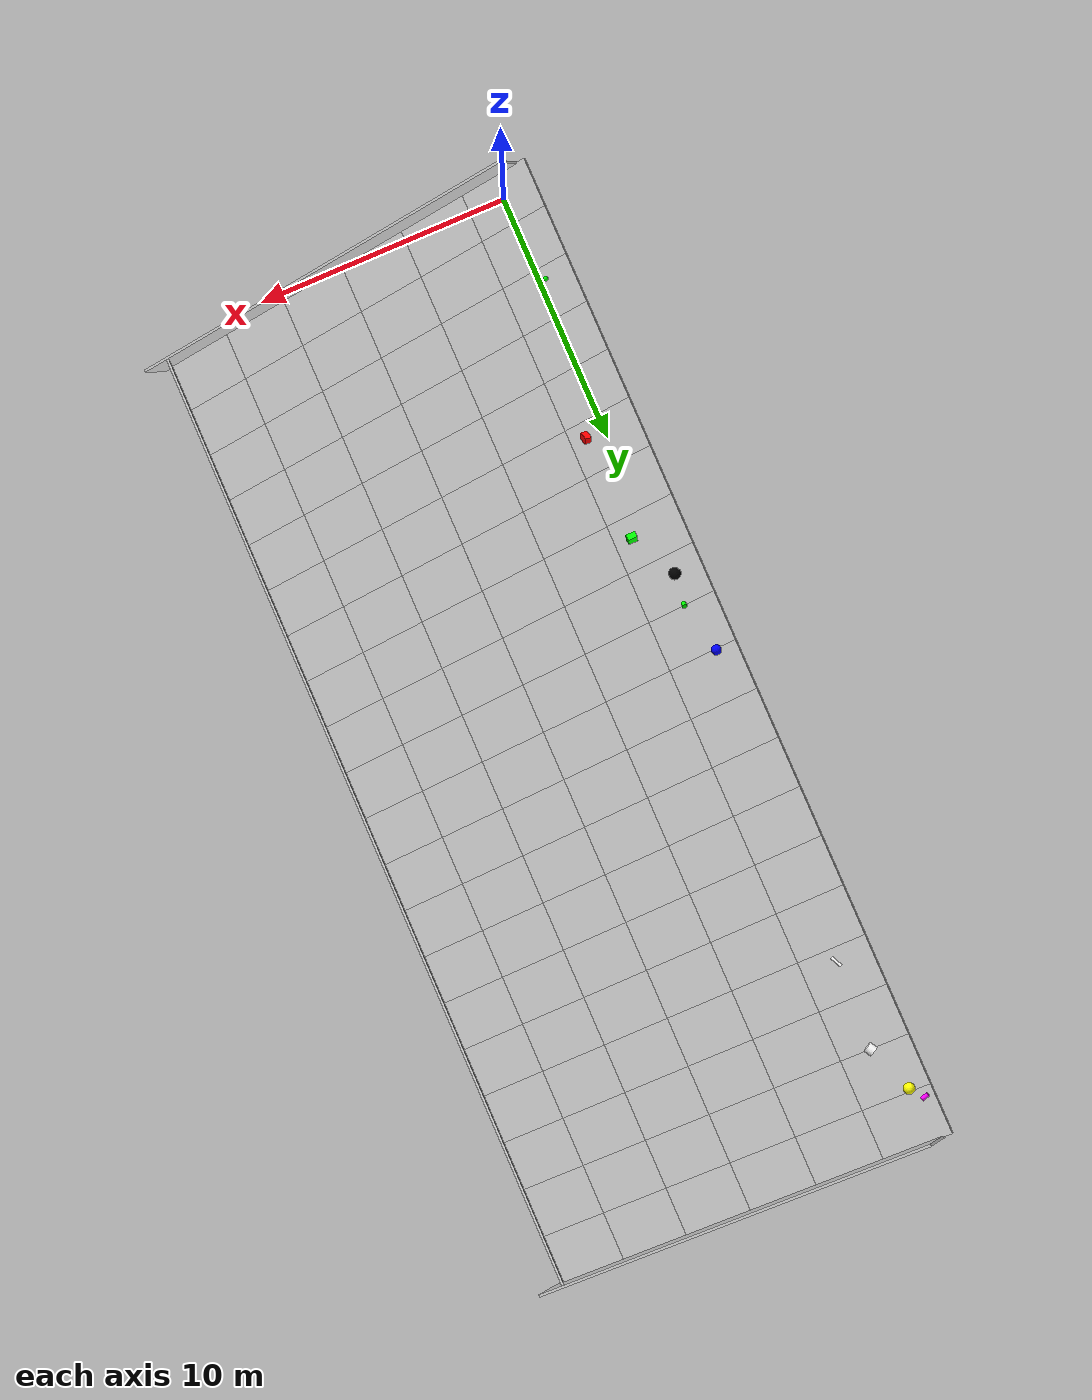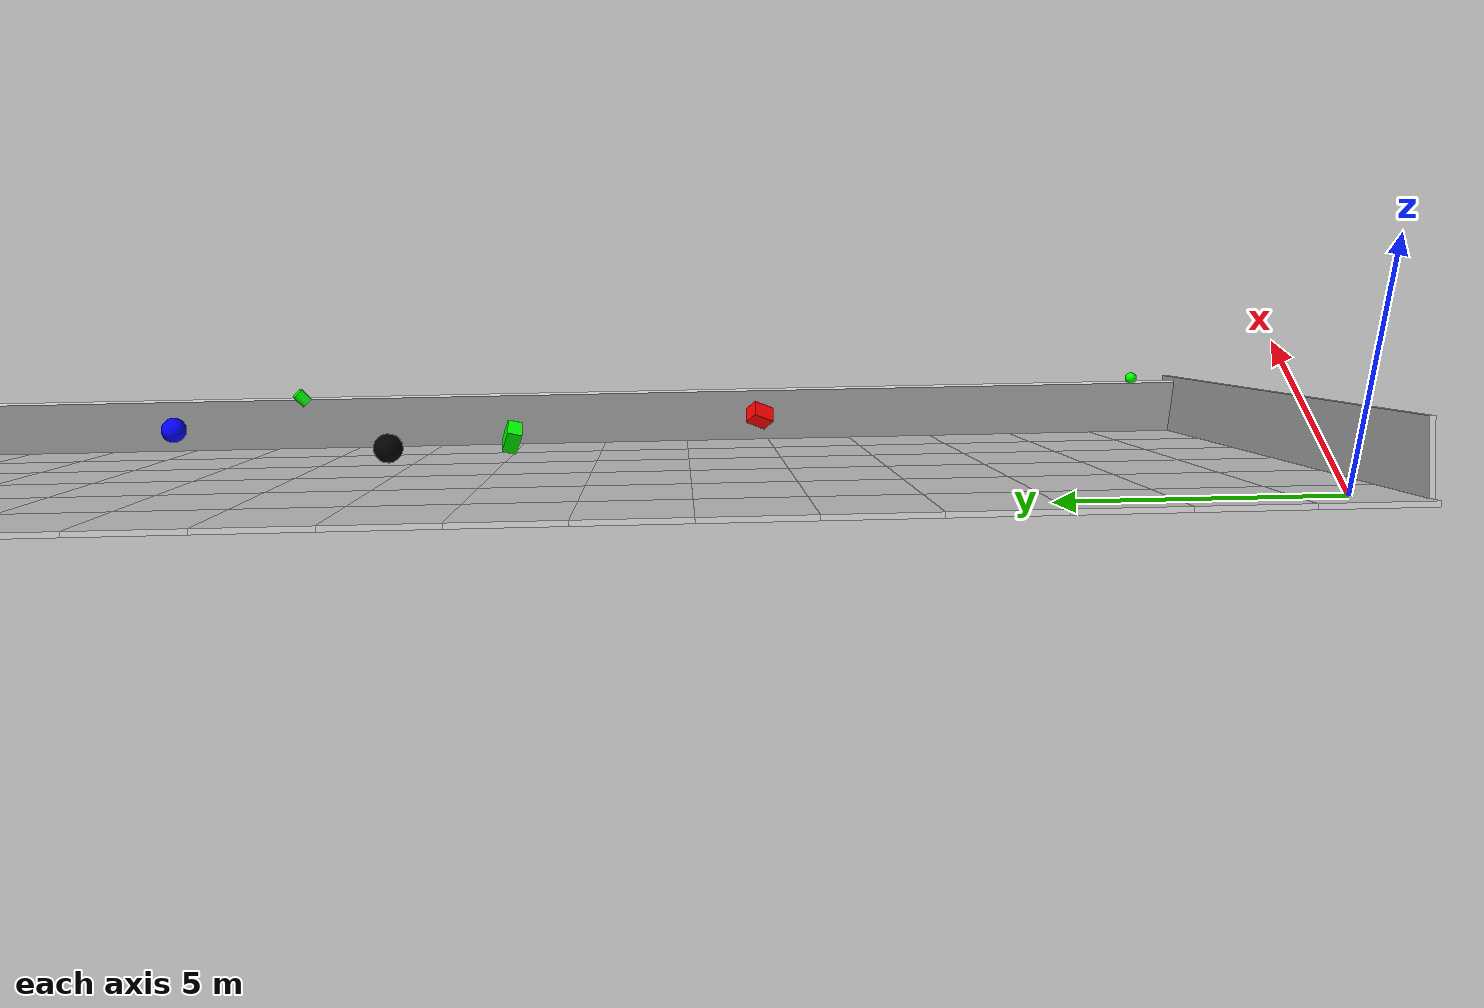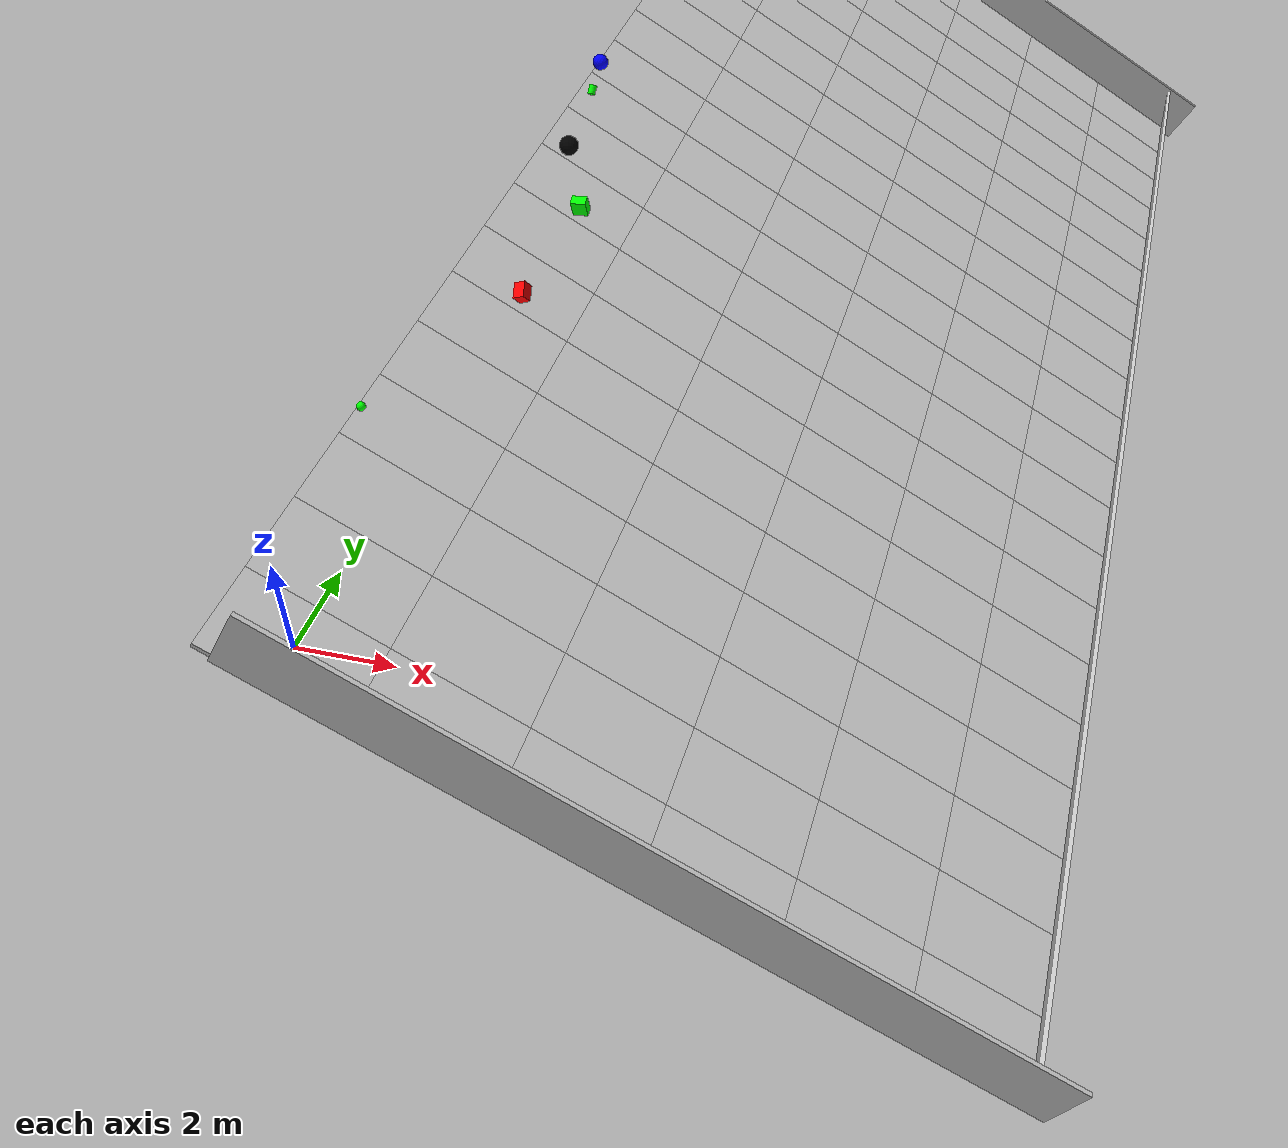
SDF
<?xml version="1.0" ?>

<!--
  Generated from distributed_rolling.erb.sdf

  - primary: false
  - secondary: true
  - performers: 10
  - seed: 34
  - fun: true
  - level visuals: false

-->
<sdf version="1.6">
  <world name="default">

    <plugin
     filename="libignition-gazebo-physics-system.so"
     name="ignition::gazebo::systems::Physics">
    </plugin>

    <scene>
      <ambient>0.8 0.8 0.8 1.0</ambient>
      <background>0.34 0.39 0.43 1.0</background>
      <grid>false</grid>
      <origin_visual>false</origin_visual>
    </scene>

    <light type="directional" name="sun">
      <cast_shadows>true</cast_shadows>
      <pose>0 0 10 0 0 0</pose>
      <diffuse>0.8 0.8 0.8 1</diffuse>
      <specular>0.2 0.2 0.2 1</specular>
      <attenuation>
        <range>1000</range>
        <constant>0.9</constant>
        <linear>0.01</linear>
        <quadratic>0.001</quadratic>
      </attenuation>
      <direction>-0.5 0.1 -0.9</direction>
    </light>

    <model name="model_1">
      <pose>
        -0.038271952556842015
        3.959762532615608
        2.462529946225647
        1.066721489782598
        1.2828383124867102
        2.5433092710002985
      </pose>
      <link name="link">
        <inertial>
      <mass>0.011222515870999929</mass>
      <inertia>
        <ixx>3.567959466566401e-05</ixx>
        <iyy>3.567959466566401e-05</iyy>
        <izz>3.567959466566401e-05</izz>
        <ixy>0.0</ixy>
        <ixz>0.0</ixz>
        <iyz>0.0</iyz>
      </inertia>
    </inertial>

        <collision name="collision">
          <geometry>
       <sphere>
         <radius>
           0.08915277099144181
         </radius>
        </sphere>
      </geometry>

        </collision>
        <visual name="visual">
          <geometry>
       <sphere>
         <radius>
           0.08915277099144181
         </radius>
        </sphere>
      </geometry>

          <material>
            <diffuse>
              0
              1
              0
              1
            </diffuse>
            <specular>
              0
              1
              0
              1
            </specular>
            <ambient>
              1
              1
              1
              1
            </ambient>
          </material>
        </visual>
      </link>
    </model>

    <model name="model_2">
      <pose>
        -0.12676382181791312
        15.906205672275762
        1.4659229326791146
        2.706385247141538
        1.0482228673604856
        1.304410164367507
      </pose>
      <link name="link">
        <inertial>
      <mass>0.122455597367965</mass>
      <inertia>
        <ixx>0.0027519343341353376</ixx>
        <iyy>0.0027519343341353376</iyy>
        <izz>0.0027519343341353376</izz>
        <ixy>0.0</ixy>
        <ixz>0.0</ixz>
        <iyz>0.0</iyz>
      </inertia>
    </inertial>

        <collision name="collision">
          <geometry>
       <sphere>
         <radius>
           0.23702803548759238
         </radius>
        </sphere>
      </geometry>

        </collision>
        <visual name="visual">
          <geometry>
       <sphere>
         <radius>
           0.23702803548759238
         </radius>
        </sphere>
      </geometry>

          <material>
            <diffuse>
              0
              0
              0
              1
            </diffuse>
            <specular>
              0
              0
              0
              1
            </specular>
            <ambient>
              0
              0
              1
              1
            </ambient>
          </material>
        </visual>
      </link>
    </model>

    <model name="model_3">
      <pose>
        -0.353857069697118
        36.77085530000893
        2.132251702737335
        2.5881195164211936
        3.0934421121878204
        2.752064684889699
      </pose>
      <link name="link">
        <inertial>
      <mass>0.1605219682343749</mass>
      <inertia>
        <ixx>0.00316656911181048</ixx>
        <iyy>0.00316656911181048</iyy>
        <izz>0.00316656911181048</izz>
        <ixy>0.0</ixy>
        <ixz>0.0</ixz>
        <iyz>0.0</iyz>
      </inertia>
    </inertial>

        <collision name="collision">
          <geometry>
       <sphere>
         <radius>
           0.22207376307411114
         </radius>
        </sphere>
      </geometry>

        </collision>
        <visual name="visual">
          <geometry>
       <sphere>
         <radius>
           0.22207376307411114
         </radius>
        </sphere>
      </geometry>

          <material>
            <diffuse>
              1
              1
              0
              1
            </diffuse>
            <specular>
              0
              0
              0
              1
            </specular>
            <ambient>
              1
              0
              0
              1
            </ambient>
          </material>
        </visual>
      </link>
    </model>

    <model name="model_4">
      <pose>
        0.25562835703222775
        31.48790306413263
        2.454026162642254
        1.6109150502920049
        0.4844041277486058
        0.47663894841040116
      </pose>
      <link name="link">
        <inertial>
      <mass>0.0010997454857456105</mass>
      <inertia>
        <ixx>2.0701124029596154e-05</ixx>
        <iyy>2.0701124029596154e-05</iyy>
        <izz>1.7666730811801447e-06</izz>
        <ixy>0.0</ixy>
        <ixz>0.0</ixz>
        <iyz>0.0</iyz>
      </inertia>
    </inertial>

        <collision name="collision">
          <geometry>
       <cylinder>
         <radius>
           0.05668223936332868
         </radius>
         <length>
           0.46502051476608375
         </length>
        </cylinder>
      </geometry>

        </collision>
        <visual name="visual">
          <geometry>
       <cylinder>
         <radius>
           0.05668223936332868
         </radius>
         <length>
           0.46502051476608375
         </length>
        </cylinder>
      </geometry>

          <material>
            <diffuse>
              1
              1
              1
              1
            </diffuse>
            <specular>
              0
              1
              1
              1
            </specular>
            <ambient>
              1
              1
              1
              1
            </ambient>
          </material>
        </visual>
      </link>
    </model>

    <model name="model_5">
      <pose>
        0.1006548400403221
        17.21287808213079
        2.3141409388962617
        3.0284407605036097
        0.7237282130935071
        1.246580234347236
      </pose>
      <link name="link">
        <inertial>
      <mass>0.019406978406939474</mass>
      <inertia>
        <ixx>0.00011904788369320333</ixx>
        <iyy>0.00011904788369320333</iyy>
        <izz>8.277062895178454e-05</izz>
        <ixy>0.0</ixy>
        <ixz>0.0</ixz>
        <iyz>0.0</iyz>
      </inertia>
    </inertial>

        <collision name="collision">
          <geometry>
       <cylinder>
         <radius>
           0.09235792437736104
         </radius>
         <length>
           0.21913792172734095
         </length>
        </cylinder>
      </geometry>

        </collision>
        <visual name="visual">
          <geometry>
       <cylinder>
         <radius>
           0.09235792437736104
         </radius>
         <length>
           0.21913792172734095
         </length>
        </cylinder>
      </geometry>

          <material>
            <diffuse>
              0
              1
              0
              1
            </diffuse>
            <specular>
              1
              1
              1
              1
            </specular>
            <ambient>
              0
              1
              0
              1
            </ambient>
          </material>
        </visual>
      </link>
    </model>

    <model name="model_6">
      <pose>
        -0.7681961952192605
        37.279755310238826
        2.120098301978966
        2.7999701416333806
        1.311916980899421
        3.0705459351184587
      </pose>
      <link name="link">
        <inertial>
      <mass>0.014166372268568886</mass>
      <inertia>
        <ixx>0.0001238716603329791</ixx>
        <iyy>0.0001238716603329791</iyy>
        <izz>5.612482599677863e-05</izz>
        <ixy>0.0</ixy>
        <ixz>0.0</ixz>
        <iyz>0.0</iyz>
      </inertia>
    </inertial>

        <collision name="collision">
          <geometry>
       <cylinder>
         <radius>
           0.0890149959766019
         </radius>
         <length>
           0.28488200166596106
         </length>
        </cylinder>
      </geometry>

        </collision>
        <visual name="visual">
          <geometry>
       <cylinder>
         <radius>
           0.0890149959766019
         </radius>
         <length>
           0.28488200166596106
         </length>
        </cylinder>
      </geometry>

          <material>
            <diffuse>
              1
              0
              1
              1
            </diffuse>
            <specular>
              0
              1
              1
              1
            </specular>
            <ambient>
              1
              1
              0
              1
            </ambient>
          </material>
        </visual>
      </link>
    </model>

    <model name="model_7">
      <pose>
        -0.35216568778221485
        19.194924710673952
        2.0448916751496973
        2.8281247883208547
        1.086383983744296
        2.708711065051292
      </pose>
      <link name="link">
        <inertial>
      <mass>0.08879607765681512</mass>
      <inertia>
        <ixx>0.0013709341070548317</ixx>
        <iyy>0.0013709341070548317</iyy>
        <izz>0.0013709341070548317</izz>
        <ixy>0.0</ixy>
        <ixz>0.0</ixz>
        <iyz>0.0</iyz>
      </inertia>
    </inertial>

        <collision name="collision">
          <geometry>
       <sphere>
         <radius>
           0.1964632860489126
         </radius>
        </sphere>
      </geometry>

        </collision>
        <visual name="visual">
          <geometry>
       <sphere>
         <radius>
           0.1964632860489126
         </radius>
        </sphere>
      </geometry>

          <material>
            <diffuse>
              0
              0
              1
              1
            </diffuse>
            <specular>
              0
              1
              0
              1
            </specular>
            <ambient>
              0
              0
              0
              1
            </ambient>
          </material>
        </visual>
      </link>
    </model>

    <model name="model_8">
      <pose>
        0.7767954464235158
        13.991533947986316
        1.029149445295319
        1.620926287593392
        2.842830134354316
        1.616057043043007
      </pose>
      <link name="link">
        <inertial>
      <mass>0.08261027453007969</mass>
      <inertia>
        <ixx>0.002014914596640963</ixx>
        <iyy>0.0013454234872722533</iyy>
        <izz>0.0014988091572397978</izz>
        <ixy>0.0</ixy>
        <ixz>0.0</ixz>
        <iyz>0.0</iyz>
      </inertia>
    </inertial>

        <collision name="collision">
          <geometry>
       <box>
         <size>
           0.24542519845996835
           0.39684261621582184
           0.36769987911048974
         </size>
        </box>
      </geometry>

        </collision>
        <visual name="visual">
          <geometry>
       <box>
         <size>
           0.24542519845996835
           0.39684261621582184
           0.36769987911048974
         </size>
        </box>
      </geometry>

          <material>
            <diffuse>
              0
              1
              0
              1
            </diffuse>
            <specular>
              0
              0
              0
              1
            </specular>
            <ambient>
              1
              0
              1
              1
            </ambient>
          </material>
        </visual>
      </link>
    </model>

    <model name="model_9">
      <pose>
        0.26346041130565445
        34.95744530427965
        1.0065088582934987
        1.4054825645249964
        1.454456644537457
        0.3821552857763127
      </pose>
      <link name="link">
        <inertial>
      <mass>0.13362260983026794</mass>
      <inertia>
        <ixx>0.0025017873766614517</ixx>
        <iyy>0.0025017873766614517</iyy>
        <izz>0.002927181712060923</izz>
        <ixy>0.0</ixy>
        <ixz>0.0</ixz>
        <iyz>0.0</iyz>
      </inertia>
    </inertial>

        <collision name="collision">
          <geometry>
       <cylinder>
         <radius>
           0.20931476503415386
         </radius>
         <length>
           0.3053447326711294
         </length>
        </cylinder>
      </geometry>

        </collision>
        <visual name="visual">
          <geometry>
       <cylinder>
         <radius>
           0.20931476503415386
         </radius>
         <length>
           0.3053447326711294
         </length>
        </cylinder>
      </geometry>

          <material>
            <diffuse>
              1
              1
              1
              1
            </diffuse>
            <specular>
              0
              0
              1
              1
            </specular>
            <ambient>
              1
              1
              1
              1
            </ambient>
          </material>
        </visual>
      </link>
    </model>

    <model name="model_10">
      <pose>
        0.8658046214067792
        9.868357803020617
        1.3044535573637759
        0.9412412023747528
        0.9010714836349217
        0.9969421995681935
      </pose>
      <link name="link">
        <inertial>
      <mass>0.007915386322146037</mass>
      <inertia>
        <ixx>0.00013824236259011782</ixx>
        <iyy>9.739401543267154e-05</iyy>
        <izz>0.00013895046738993761</izz>
        <ixy>0.0</ixy>
        <ixz>0.0</ixz>
        <iyz>0.0</iyz>
      </inertia>
    </inertial>

        <collision name="collision">
          <geometry>
       <box>
         <size>
           0.27269599772218023
           0.3691755912948558
           0.2707205122544274
         </size>
        </box>
      </geometry>

        </collision>
        <visual name="visual">
          <geometry>
       <box>
         <size>
           0.27269599772218023
           0.3691755912948558
           0.2707205122544274
         </size>
        </box>
      </geometry>

          <material>
            <diffuse>
              1
              0
              0
              1
            </diffuse>
            <specular>
              0
              0
              1
              1
            </specular>
            <ambient>
              0
              0
              1
              1
            </ambient>
          </material>
        </visual>
      </link>
    </model>

    <model name="block_0_0">
      <static>true</static>
      <pose>0.0 0.0 -0.0 0 0.5235987755982988 0</pose>
      <link name="link">
        <collision name="collision">
          <geometry>
       <box>
         <size>
           3.0
           2.0
           0.1
         </size>
        </box>
      </geometry>

        </collision>
        <visual name="visual">
          <geometry>
       <box>
         <size>
           3.0
           2.0
           0.1
         </size>
        </box>
      </geometry>

          <material>
            <ambient>0.8 0.8 0.8 1</ambient>
            <diffuse>0.8 0.8 0.8 1</diffuse>
            <specular>0.8 0.8 0.8 1</specular>
          </material>
        </visual>
      </link>
    </model>

    <model name="block_0_1">
      <static>true</static>
      <pose>0.0 2.0 -0.0 0 0.5235987755982988 0</pose>
      <link name="link">
        <collision name="collision">
          <geometry>
       <box>
         <size>
           3.0
           2.0
           0.1
         </size>
        </box>
      </geometry>

        </collision>
        <visual name="visual">
          <geometry>
       <box>
         <size>
           3.0
           2.0
           0.1
         </size>
        </box>
      </geometry>

          <material>
            <ambient>0.8 0.8 0.8 1</ambient>
            <diffuse>0.8 0.8 0.8 1</diffuse>
            <specular>0.8 0.8 0.8 1</specular>
          </material>
        </visual>
      </link>
    </model>

    <model name="block_0_2">
      <static>true</static>
      <pose>0.0 4.0 -0.0 0 0.5235987755982988 0</pose>
      <link name="link">
        <collision name="collision">
          <geometry>
       <box>
         <size>
           3.0
           2.0
           0.1
         </size>
        </box>
      </geometry>

        </collision>
        <visual name="visual">
          <geometry>
       <box>
         <size>
           3.0
           2.0
           0.1
         </size>
        </box>
      </geometry>

          <material>
            <ambient>0.8 0.8 0.8 1</ambient>
            <diffuse>0.8 0.8 0.8 1</diffuse>
            <specular>0.8 0.8 0.8 1</specular>
          </material>
        </visual>
      </link>
    </model>

    <model name="block_0_3">
      <static>true</static>
      <pose>0.0 6.0 -0.0 0 0.5235987755982988 0</pose>
      <link name="link">
        <collision name="collision">
          <geometry>
       <box>
         <size>
           3.0
           2.0
           0.1
         </size>
        </box>
      </geometry>

        </collision>
        <visual name="visual">
          <geometry>
       <box>
         <size>
           3.0
           2.0
           0.1
         </size>
        </box>
      </geometry>

          <material>
            <ambient>0.8 0.8 0.8 1</ambient>
            <diffuse>0.8 0.8 0.8 1</diffuse>
            <specular>0.8 0.8 0.8 1</specular>
          </material>
        </visual>
      </link>
    </model>

    <model name="block_0_4">
      <static>true</static>
      <pose>0.0 8.0 -0.0 0 0.5235987755982988 0</pose>
      <link name="link">
        <collision name="collision">
          <geometry>
       <box>
         <size>
           3.0
           2.0
           0.1
         </size>
        </box>
      </geometry>

        </collision>
        <visual name="visual">
          <geometry>
       <box>
         <size>
           3.0
           2.0
           0.1
         </size>
        </box>
      </geometry>

          <material>
            <ambient>0.8 0.8 0.8 1</ambient>
            <diffuse>0.8 0.8 0.8 1</diffuse>
            <specular>0.8 0.8 0.8 1</specular>
          </material>
        </visual>
      </link>
    </model>

    <model name="block_0_5">
      <static>true</static>
      <pose>0.0 10.0 -0.0 0 0.5235987755982988 0</pose>
      <link name="link">
        <collision name="collision">
          <geometry>
       <box>
         <size>
           3.0
           2.0
           0.1
         </size>
        </box>
      </geometry>

        </collision>
        <visual name="visual">
          <geometry>
       <box>
         <size>
           3.0
           2.0
           0.1
         </size>
        </box>
      </geometry>

          <material>
            <ambient>0.8 0.8 0.8 1</ambient>
            <diffuse>0.8 0.8 0.8 1</diffuse>
            <specular>0.8 0.8 0.8 1</specular>
          </material>
        </visual>
      </link>
    </model>

    <model name="block_0_6">
      <static>true</static>
      <pose>0.0 12.0 -0.0 0 0.5235987755982988 0</pose>
      <link name="link">
        <collision name="collision">
          <geometry>
       <box>
         <size>
           3.0
           2.0
           0.1
         </size>
        </box>
      </geometry>

        </collision>
        <visual name="visual">
          <geometry>
       <box>
         <size>
           3.0
           2.0
           0.1
         </size>
        </box>
      </geometry>

          <material>
            <ambient>0.8 0.8 0.8 1</ambient>
            <diffuse>0.8 0.8 0.8 1</diffuse>
            <specular>0.8 0.8 0.8 1</specular>
          </material>
        </visual>
      </link>
    </model>

    <model name="block_0_7">
      <static>true</static>
      <pose>0.0 14.0 -0.0 0 0.5235987755982988 0</pose>
      <link name="link">
        <collision name="collision">
          <geometry>
       <box>
         <size>
           3.0
           2.0
           0.1
         </size>
        </box>
      </geometry>

        </collision>
        <visual name="visual">
          <geometry>
       <box>
         <size>
           3.0
           2.0
           0.1
         </size>
        </box>
      </geometry>

          <material>
            <ambient>0.8 0.8 0.8 1</ambient>
            <diffuse>0.8 0.8 0.8 1</diffuse>
            <specular>0.8 0.8 0.8 1</specular>
          </material>
        </visual>
      </link>
    </model>

    <model name="block_0_8">
      <static>true</static>
      <pose>0.0 16.0 -0.0 0 0.5235987755982988 0</pose>
      <link name="link">
        <collision name="collision">
          <geometry>
       <box>
         <size>
           3.0
           2.0
           0.1
         </size>
        </box>
      </geometry>

        </collision>
        <visual name="visual">
          <geometry>
       <box>
         <size>
           3.0
           2.0
           0.1
         </size>
        </box>
      </geometry>

          <material>
            <ambient>0.8 0.8 0.8 1</ambient>
            <diffuse>0.8 0.8 0.8 1</diffuse>
            <specular>0.8 0.8 0.8 1</specular>
          </material>
        </visual>
      </link>
    </model>

    <model name="block_0_9">
      <static>true</static>
      <pose>0.0 18.0 -0.0 0 0.5235987755982988 0</pose>
      <link name="link">
        <collision name="collision">
          <geometry>
       <box>
         <size>
           3.0
           2.0
           0.1
         </size>
        </box>
      </geometry>

        </collision>
        <visual name="visual">
          <geometry>
       <box>
         <size>
           3.0
           2.0
           0.1
         </size>
        </box>
      </geometry>

          <material>
            <ambient>0.8 0.8 0.8 1</ambient>
            <diffuse>0.8 0.8 0.8 1</diffuse>
            <specular>0.8 0.8 0.8 1</specular>
          </material>
        </visual>
      </link>
    </model>

    <model name="block_0_10">
      <static>true</static>
      <pose>0.0 20.0 -0.0 0 0.5235987755982988 0</pose>
      <link name="link">
        <collision name="collision">
          <geometry>
       <box>
         <size>
           3.0
           2.0
           0.1
         </size>
        </box>
      </geometry>

        </collision>
        <visual name="visual">
          <geometry>
       <box>
         <size>
           3.0
           2.0
           0.1
         </size>
        </box>
      </geometry>

          <material>
            <ambient>0.8 0.8 0.8 1</ambient>
            <diffuse>0.8 0.8 0.8 1</diffuse>
            <specular>0.8 0.8 0.8 1</specular>
          </material>
        </visual>
      </link>
    </model>

    <model name="block_0_11">
      <static>true</static>
      <pose>0.0 22.0 -0.0 0 0.5235987755982988 0</pose>
      <link name="link">
        <collision name="collision">
          <geometry>
       <box>
         <size>
           3.0
           2.0
           0.1
         </size>
        </box>
      </geometry>

        </collision>
        <visual name="visual">
          <geometry>
       <box>
         <size>
           3.0
           2.0
           0.1
         </size>
        </box>
      </geometry>

          <material>
            <ambient>0.8 0.8 0.8 1</ambient>
            <diffuse>0.8 0.8 0.8 1</diffuse>
            <specular>0.8 0.8 0.8 1</specular>
          </material>
        </visual>
      </link>
    </model>

    <model name="block_0_12">
      <static>true</static>
      <pose>0.0 24.0 -0.0 0 0.5235987755982988 0</pose>
      <link name="link">
        <collision name="collision">
          <geometry>
       <box>
         <size>
           3.0
           2.0
           0.1
         </size>
        </box>
      </geometry>

        </collision>
        <visual name="visual">
          <geometry>
       <box>
         <size>
           3.0
           2.0
           0.1
         </size>
        </box>
      </geometry>

          <material>
            <ambient>0.8 0.8 0.8 1</ambient>
            <diffuse>0.8 0.8 0.8 1</diffuse>
            <specular>0.8 0.8 0.8 1</specular>
          </material>
        </visual>
      </link>
    </model>

    <model name="block_0_13">
      <static>true</static>
      <pose>0.0 26.0 -0.0 0 0.5235987755982988 0</pose>
      <link name="link">
        <collision name="collision">
          <geometry>
       <box>
         <size>
           3.0
           2.0
           0.1
         </size>
        </box>
      </geometry>

        </collision>
        <visual name="visual">
          <geometry>
       <box>
         <size>
           3.0
           2.0
           0.1
         </size>
        </box>
      </geometry>

          <material>
            <ambient>0.8 0.8 0.8 1</ambient>
            <diffuse>0.8 0.8 0.8 1</diffuse>
            <specular>0.8 0.8 0.8 1</specular>
          </material>
        </visual>
      </link>
    </model>

    <model name="block_0_14">
      <static>true</static>
      <pose>0.0 28.0 -0.0 0 0.5235987755982988 0</pose>
      <link name="link">
        <collision name="collision">
          <geometry>
       <box>
         <size>
           3.0
           2.0
           0.1
         </size>
        </box>
      </geometry>

        </collision>
        <visual name="visual">
          <geometry>
       <box>
         <size>
           3.0
           2.0
           0.1
         </size>
        </box>
      </geometry>

          <material>
            <ambient>0.8 0.8 0.8 1</ambient>
            <diffuse>0.8 0.8 0.8 1</diffuse>
            <specular>0.8 0.8 0.8 1</specular>
          </material>
        </visual>
      </link>
    </model>

    <model name="block_0_15">
      <static>true</static>
      <pose>0.0 30.0 -0.0 0 0.5235987755982988 0</pose>
      <link name="link">
        <collision name="collision">
          <geometry>
       <box>
         <size>
           3.0
           2.0
           0.1
         </size>
        </box>
      </geometry>

        </collision>
        <visual name="visual">
          <geometry>
       <box>
         <size>
           3.0
           2.0
           0.1
         </size>
        </box>
      </geometry>

          <material>
            <ambient>0.8 0.8 0.8 1</ambient>
            <diffuse>0.8 0.8 0.8 1</diffuse>
            <specular>0.8 0.8 0.8 1</specular>
          </material>
        </visual>
      </link>
    </model>

    <model name="block_0_16">
      <static>true</static>
      <pose>0.0 32.0 -0.0 0 0.5235987755982988 0</pose>
      <link name="link">
        <collision name="collision">
          <geometry>
       <box>
         <size>
           3.0
           2.0
           0.1
         </size>
        </box>
      </geometry>

        </collision>
        <visual name="visual">
          <geometry>
       <box>
         <size>
           3.0
           2.0
           0.1
         </size>
        </box>
      </geometry>

          <material>
            <ambient>0.8 0.8 0.8 1</ambient>
            <diffuse>0.8 0.8 0.8 1</diffuse>
            <specular>0.8 0.8 0.8 1</specular>
          </material>
        </visual>
      </link>
    </model>

    <model name="block_0_17">
      <static>true</static>
      <pose>0.0 34.0 -0.0 0 0.5235987755982988 0</pose>
      <link name="link">
        <collision name="collision">
          <geometry>
       <box>
         <size>
           3.0
           2.0
           0.1
         </size>
        </box>
      </geometry>

        </collision>
        <visual name="visual">
          <geometry>
       <box>
         <size>
           3.0
           2.0
           0.1
         </size>
        </box>
      </geometry>

          <material>
            <ambient>0.8 0.8 0.8 1</ambient>
            <diffuse>0.8 0.8 0.8 1</diffuse>
            <specular>0.8 0.8 0.8 1</specular>
          </material>
        </visual>
      </link>
    </model>

    <model name="block_0_18">
      <static>true</static>
      <pose>0.0 36.0 -0.0 0 0.5235987755982988 0</pose>
      <link name="link">
        <collision name="collision">
          <geometry>
       <box>
         <size>
           3.0
           2.0
           0.1
         </size>
        </box>
      </geometry>

        </collision>
        <visual name="visual">
          <geometry>
       <box>
         <size>
           3.0
           2.0
           0.1
         </size>
        </box>
      </geometry>

          <material>
            <ambient>0.8 0.8 0.8 1</ambient>
            <diffuse>0.8 0.8 0.8 1</diffuse>
            <specular>0.8 0.8 0.8 1</specular>
          </material>
        </visual>
      </link>
    </model>

    <model name="block_0_19">
      <static>true</static>
      <pose>0.0 38.0 -0.0 0 0.5235987755982988 0</pose>
      <link name="link">
        <collision name="collision">
          <geometry>
       <box>
         <size>
           3.0
           2.0
           0.1
         </size>
        </box>
      </geometry>

        </collision>
        <visual name="visual">
          <geometry>
       <box>
         <size>
           3.0
           2.0
           0.1
         </size>
        </box>
      </geometry>

          <material>
            <ambient>0.8 0.8 0.8 1</ambient>
            <diffuse>0.8 0.8 0.8 1</diffuse>
            <specular>0.8 0.8 0.8 1</specular>
          </material>
        </visual>
      </link>
    </model>

    <model name="block_1_0">
      <static>true</static>
      <pose>2.598076211353316 0.0 -1.4999999999999998 0 0.5235987755982988 0</pose>
      <link name="link">
        <collision name="collision">
          <geometry>
       <box>
         <size>
           3.0
           2.0
           0.1
         </size>
        </box>
      </geometry>

        </collision>
        <visual name="visual">
          <geometry>
       <box>
         <size>
           3.0
           2.0
           0.1
         </size>
        </box>
      </geometry>

          <material>
            <ambient>0.8 0.8 0.8 1</ambient>
            <diffuse>0.8 0.8 0.8 1</diffuse>
            <specular>0.8 0.8 0.8 1</specular>
          </material>
        </visual>
      </link>
    </model>

    <model name="block_1_1">
      <static>true</static>
      <pose>2.598076211353316 2.0 -1.4999999999999998 0 0.5235987755982988 0</pose>
      <link name="link">
        <collision name="collision">
          <geometry>
       <box>
         <size>
           3.0
           2.0
           0.1
         </size>
        </box>
      </geometry>

        </collision>
        <visual name="visual">
          <geometry>
       <box>
         <size>
           3.0
           2.0
           0.1
         </size>
        </box>
      </geometry>

          <material>
            <ambient>0.8 0.8 0.8 1</ambient>
            <diffuse>0.8 0.8 0.8 1</diffuse>
            <specular>0.8 0.8 0.8 1</specular>
          </material>
        </visual>
      </link>
    </model>

    <model name="block_1_2">
      <static>true</static>
      <pose>2.598076211353316 4.0 -1.4999999999999998 0 0.5235987755982988 0</pose>
      <link name="link">
        <collision name="collision">
          <geometry>
       <box>
         <size>
           3.0
           2.0
           0.1
         </size>
        </box>
      </geometry>

        </collision>
        <visual name="visual">
          <geometry>
       <box>
         <size>
           3.0
           2.0
           0.1
         </size>
        </box>
      </geometry>

          <material>
            <ambient>0.8 0.8 0.8 1</ambient>
            <diffuse>0.8 0.8 0.8 1</diffuse>
            <specular>0.8 0.8 0.8 1</specular>
          </material>
        </visual>
      </link>
    </model>

    <model name="block_1_3">
      <static>true</static>
      <pose>2.598076211353316 6.0 -1.4999999999999998 0 0.5235987755982988 0</pose>
      <link name="link">
        <collision name="collision">
          <geometry>
       <box>
         <size>
           3.0
           2.0
           0.1
         </size>
        </box>
      </geometry>

        </collision>
        <visual name="visual">
          <geometry>
       <box>
         <size>
           3.0
           2.0
           0.1
         </size>
        </box>
      </geometry>

          <material>
            <ambient>0.8 0.8 0.8 1</ambient>
            <diffuse>0.8 0.8 0.8 1</diffuse>
            <specular>0.8 0.8 0.8 1</specular>
          </material>
        </visual>
      </link>
    </model>

    <model name="block_1_4">
      <static>true</static>
      <pose>2.598076211353316 8.0 -1.4999999999999998 0 0.5235987755982988 0</pose>
      <link name="link">
        <collision name="collision">
          <geometry>
       <box>
         <size>
           3.0
           2.0
           0.1
         </size>
        </box>
      </geometry>

        </collision>
        <visual name="visual">
          <geometry>
       <box>
         <size>
           3.0
           2.0
           0.1
         </size>
        </box>
      </geometry>

          <material>
            <ambient>0.8 0.8 0.8 1</ambient>
            <diffuse>0.8 0.8 0.8 1</diffuse>
            <specular>0.8 0.8 0.8 1</specular>
          </material>
        </visual>
      </link>
    </model>

    <model name="block_1_5">
      <static>true</static>
      <pose>2.598076211353316 10.0 -1.4999999999999998 0 0.5235987755982988 0</pose>
      <link name="link">
        <collision name="collision">
          <geometry>
       <box>
         <size>
           3.0
           2.0
           0.1
         </size>
        </box>
      </geometry>

        </collision>
        <visual name="visual">
          <geometry>
       <box>
         <size>
           3.0
           2.0
           0.1
         </size>
        </box>
      </geometry>

          <material>
            <ambient>0.8 0.8 0.8 1</ambient>
            <diffuse>0.8 0.8 0.8 1</diffuse>
            <specular>0.8 0.8 0.8 1</specular>
          </material>
        </visual>
      </link>
    </model>

    <model name="block_1_6">
      <static>true</static>
      <pose>2.598076211353316 12.0 -1.4999999999999998 0 0.5235987755982988 0</pose>
      <link name="link">
        <collision name="collision">
          <geometry>
       <box>
         <size>
           3.0
           2.0
           0.1
         </size>
        </box>
      </geometry>

        </collision>
        <visual name="visual">
          <geometry>
       <box>
         <size>
           3.0
           2.0
           0.1
         </size>
        </box>
      </geometry>

          <material>
            <ambient>0.8 0.8 0.8 1</ambient>
            <diffuse>0.8 0.8 0.8 1</diffuse>
            <specular>0.8 0.8 0.8 1</specular>
          </material>
        </visual>
      </link>
    </model>

    <model name="block_1_7">
      <static>true</static>
      <pose>2.598076211353316 14.0 -1.4999999999999998 0 0.5235987755982988 0</pose>
      <link name="link">
        <collision name="collision">
          <geometry>
       <box>
         <size>
           3.0
           2.0
           0.1
         </size>
        </box>
      </geometry>

        </collision>
        <visual name="visual">
          <geometry>
       <box>
         <size>
           3.0
           2.0
           0.1
         </size>
        </box>
      </geometry>

          <material>
            <ambient>0.8 0.8 0.8 1</ambient>
            <diffuse>0.8 0.8 0.8 1</diffuse>
            <specular>0.8 0.8 0.8 1</specular>
          </material>
        </visual>
      </link>
    </model>

    <model name="block_1_8">
      <static>true</static>
      <pose>2.598076211353316 16.0 -1.4999999999999998 0 0.5235987755982988 0</pose>
      <link name="link">
        <collision name="collision">
          <geometry>
       <box>
         <size>
           3.0
           2.0
           0.1
         </size>
        </box>
      </geometry>

        </collision>
        <visual name="visual">
          <geometry>
       <box>
         <size>
           3.0
           2.0
           0.1
         </size>
        </box>
      </geometry>

          <material>
            <ambient>0.8 0.8 0.8 1</ambient>
            <diffuse>0.8 0.8 0.8 1</diffuse>
            <specular>0.8 0.8 0.8 1</specular>
          </material>
        </visual>
      </link>
    </model>

    <model name="block_1_9">
      <static>true</static>
      <pose>2.598076211353316 18.0 -1.4999999999999998 0 0.5235987755982988 0</pose>
      <link name="link">
        <collision name="collision">
          <geometry>
       <box>
         <size>
           3.0
           2.0
           0.1
         </size>
        </box>
      </geometry>

        </collision>
        <visual name="visual">
          <geometry>
       <box>
         <size>
           3.0
           2.0
           0.1
         </size>
        </box>
      </geometry>

          <material>
            <ambient>0.8 0.8 0.8 1</ambient>
            <diffuse>0.8 0.8 0.8 1</diffuse>
            <specular>0.8 0.8 0.8 1</specular>
          </material>
        </visual>
      </link>
    </model>

    <model name="block_1_10">
      <static>true</static>
      <pose>2.598076211353316 20.0 -1.4999999999999998 0 0.5235987755982988 0</pose>
      <link name="link">
        <collision name="collision">
          <geometry>
       <box>
         <size>
           3.0
           2.0
           0.1
         </size>
        </box>
      </geometry>

        </collision>
        <visual name="visual">
          <geometry>
       <box>
         <size>
           3.0
           2.0
           0.1
         </size>
        </box>
      </geometry>

          <material>
            <ambient>0.8 0.8 0.8 1</ambient>
            <diffuse>0.8 0.8 0.8 1</diffuse>
            <specular>0.8 0.8 0.8 1</specular>
          </material>
        </visual>
      </link>
    </model>

    <model name="block_1_11">
      <static>true</static>
      <pose>2.598076211353316 22.0 -1.4999999999999998 0 0.5235987755982988 0</pose>
      <link name="link">
        <collision name="collision">
          <geometry>
       <box>
         <size>
           3.0
           2.0
           0.1
         </size>
        </box>
      </geometry>

        </collision>
        <visual name="visual">
          <geometry>
       <box>
         <size>
           3.0
           2.0
           0.1
         </size>
        </box>
      </geometry>

          <material>
            <ambient>0.8 0.8 0.8 1</ambient>
            <diffuse>0.8 0.8 0.8 1</diffuse>
            <specular>0.8 0.8 0.8 1</specular>
          </material>
        </visual>
      </link>
    </model>

    <model name="block_1_12">
      <static>true</static>
      <pose>2.598076211353316 24.0 -1.4999999999999998 0 0.5235987755982988 0</pose>
      <link name="link">
        <collision name="collision">
          <geometry>
       <box>
         <size>
           3.0
           2.0
           0.1
         </size>
        </box>
      </geometry>

        </collision>
        <visual name="visual">
          <geometry>
       <box>
         <size>
           3.0
           2.0
           0.1
         </size>
        </box>
      </geometry>

          <material>
            <ambient>0.8 0.8 0.8 1</ambient>
            <diffuse>0.8 0.8 0.8 1</diffuse>
            <specular>0.8 0.8 0.8 1</specular>
          </material>
        </visual>
      </link>
    </model>

    <model name="block_1_13">
      <static>true</static>
      <pose>2.598076211353316 26.0 -1.4999999999999998 0 0.5235987755982988 0</pose>
      <link name="link">
        <collision name="collision">
          <geometry>
       <box>
         <size>
           3.0
           2.0
           0.1
         </size>
        </box>
      </geometry>

        </collision>
        <visual name="visual">
          <geometry>
       <box>
         <size>
           3.0
           2.0
           0.1
         </size>
        </box>
      </geometry>

          <material>
            <ambient>0.8 0.8 0.8 1</ambient>
            <diffuse>0.8 0.8 0.8 1</diffuse>
            <specular>0.8 0.8 0.8 1</specular>
          </material>
        </visual>
      </link>
    </model>

    <model name="block_1_14">
      <static>true</static>
      <pose>2.598076211353316 28.0 -1.4999999999999998 0 0.5235987755982988 0</pose>
      <link name="link">
        <collision name="collision">
          <geometry>
       <box>
         <size>
           3.0
           2.0
           0.1
         </size>
        </box>
      </geometry>

        </collision>
        <visual name="visual">
          <geometry>
       <box>
         <size>
           3.0
           2.0
           0.1
         </size>
        </box>
      </geometry>

          <material>
            <ambient>0.8 0.8 0.8 1</ambient>
            <diffuse>0.8 0.8 0.8 1</diffuse>
            <specular>0.8 0.8 0.8 1</specular>
          </material>
        </visual>
      </link>
    </model>

    <model name="block_1_15">
      <static>true</static>
      <pose>2.598076211353316 30.0 -1.4999999999999998 0 0.5235987755982988 0</pose>
      <link name="link">
        <collision name="collision">
          <geometry>
       <box>
         <size>
           3.0
           2.0
           0.1
         </size>
        </box>
      </geometry>

        </collision>
        <visual name="visual">
          <geometry>
       <box>
         <size>
           3.0
           2.0
           0.1
         </size>
        </box>
      </geometry>

          <material>
            <ambient>0.8 0.8 0.8 1</ambient>
            <diffuse>0.8 0.8 0.8 1</diffuse>
            <specular>0.8 0.8 0.8 1</specular>
          </material>
        </visual>
      </link>
    </model>

    <model name="block_1_16">
      <static>true</static>
      <pose>2.598076211353316 32.0 -1.4999999999999998 0 0.5235987755982988 0</pose>
      <link name="link">
        <collision name="collision">
          <geometry>
       <box>
         <size>
           3.0
           2.0
           0.1
         </size>
        </box>
      </geometry>

        </collision>
        <visual name="visual">
          <geometry>
       <box>
         <size>
           3.0
           2.0
           0.1
         </size>
        </box>
      </geometry>

          <material>
            <ambient>0.8 0.8 0.8 1</ambient>
            <diffuse>0.8 0.8 0.8 1</diffuse>
            <specular>0.8 0.8 0.8 1</specular>
          </material>
        </visual>
      </link>
    </model>

    <model name="block_1_17">
      <static>true</static>
      <pose>2.598076211353316 34.0 -1.4999999999999998 0 0.5235987755982988 0</pose>
      <link name="link">
        <collision name="collision">
          <geometry>
       <box>
         <size>
           3.0
           2.0
           0.1
         </size>
        </box>
      </geometry>

        </collision>
        <visual name="visual">
          <geometry>
       <box>
         <size>
           3.0
           2.0
           0.1
         </size>
        </box>
      </geometry>

          <material>
            <ambient>0.8 0.8 0.8 1</ambient>
            <diffuse>0.8 0.8 0.8 1</diffuse>
            <specular>0.8 0.8 0.8 1</specular>
          </material>
        </visual>
      </link>
    </model>

    <model name="block_1_18">
      <static>true</static>
      <pose>2.598076211353316 36.0 -1.4999999999999998 0 0.5235987755982988 0</pose>
      <link name="link">
        <collision name="collision">
          <geometry>
       <box>
         <size>
           3.0
           2.0
           0.1
         </size>
        </box>
      </geometry>

        </collision>
        <visual name="visual">
          <geometry>
       <box>
         <size>
           3.0
           2.0
           0.1
         </size>
        </box>
      </geometry>

          <material>
            <ambient>0.8 0.8 0.8 1</ambient>
            <diffuse>0.8 0.8 0.8 1</diffuse>
            <specular>0.8 0.8 0.8 1</specular>
          </material>
        </visual>
      </link>
    </model>

    <model name="block_1_19">
      <static>true</static>
      <pose>2.598076211353316 38.0 -1.4999999999999998 0 0.5235987755982988 0</pose>
      <link name="link">
        <collision name="collision">
          <geometry>
       <box>
         <size>
           3.0
           2.0
           0.1
         </size>
        </box>
      </geometry>

        </collision>
        <visual name="visual">
          <geometry>
       <box>
         <size>
           3.0
           2.0
           0.1
         </size>
        </box>
      </geometry>

          <material>
            <ambient>0.8 0.8 0.8 1</ambient>
            <diffuse>0.8 0.8 0.8 1</diffuse>
            <specular>0.8 0.8 0.8 1</specular>
          </material>
        </visual>
      </link>
    </model>

    <model name="block_2_0">
      <static>true</static>
      <pose>5.196152422706632 0.0 -2.9999999999999996 0 0.5235987755982988 0</pose>
      <link name="link">
        <collision name="collision">
          <geometry>
       <box>
         <size>
           3.0
           2.0
           0.1
         </size>
        </box>
      </geometry>

        </collision>
        <visual name="visual">
          <geometry>
       <box>
         <size>
           3.0
           2.0
           0.1
         </size>
        </box>
      </geometry>

          <material>
            <ambient>0.8 0.8 0.8 1</ambient>
            <diffuse>0.8 0.8 0.8 1</diffuse>
            <specular>0.8 0.8 0.8 1</specular>
          </material>
        </visual>
      </link>
    </model>

    <model name="block_2_1">
      <static>true</static>
      <pose>5.196152422706632 2.0 -2.9999999999999996 0 0.5235987755982988 0</pose>
      <link name="link">
        <collision name="collision">
          <geometry>
       <box>
         <size>
           3.0
           2.0
           0.1
         </size>
        </box>
      </geometry>

        </collision>
        <visual name="visual">
          <geometry>
       <box>
         <size>
           3.0
           2.0
           0.1
         </size>
        </box>
      </geometry>

          <material>
            <ambient>0.8 0.8 0.8 1</ambient>
            <diffuse>0.8 0.8 0.8 1</diffuse>
            <specular>0.8 0.8 0.8 1</specular>
          </material>
        </visual>
      </link>
    </model>

    <model name="block_2_2">
      <static>true</static>
      <pose>5.196152422706632 4.0 -2.9999999999999996 0 0.5235987755982988 0</pose>
      <link name="link">
        <collision name="collision">
          <geometry>
       <box>
         <size>
           3.0
           2.0
           0.1
         </size>
        </box>
      </geometry>

        </collision>
        <visual name="visual">
          <geometry>
       <box>
         <size>
           3.0
           2.0
           0.1
         </size>
        </box>
      </geometry>

          <material>
            <ambient>0.8 0.8 0.8 1</ambient>
            <diffuse>0.8 0.8 0.8 1</diffuse>
            <specular>0.8 0.8 0.8 1</specular>
          </material>
        </visual>
      </link>
    </model>

    <model name="block_2_3">
      <static>true</static>
      <pose>5.196152422706632 6.0 -2.9999999999999996 0 0.5235987755982988 0</pose>
      <link name="link">
        <collision name="collision">
          <geometry>
       <box>
         <size>
           3.0
           2.0
           0.1
         </size>
        </box>
      </geometry>

        </collision>
        <visual name="visual">
          <geometry>
       <box>
         <size>
           3.0
           2.0
           0.1
         </size>
        </box>
      </geometry>

          <material>
            <ambient>0.8 0.8 0.8 1</ambient>
            <diffuse>0.8 0.8 0.8 1</diffuse>
            <specular>0.8 0.8 0.8 1</specular>
          </material>
        </visual>
      </link>
    </model>

    <model name="block_2_4">
      <static>true</static>
      <pose>5.196152422706632 8.0 -2.9999999999999996 0 0.5235987755982988 0</pose>
      <link name="link">
        <collision name="collision">
          <geometry>
       <box>
         <size>
           3.0
           2.0
           0.1
         </size>
        </box>
      </geometry>

        </collision>
        <visual name="visual">
          <geometry>
       <box>
         <size>
           3.0
           2.0
           0.1
         </size>
        </box>
      </geometry>

          <material>
            <ambient>0.8 0.8 0.8 1</ambient>
            <diffuse>0.8 0.8 0.8 1</diffuse>
            <specular>0.8 0.8 0.8 1</specular>
          </material>
        </visual>
      </link>
    </model>

    <model name="block_2_5">
      <static>true</static>
      <pose>5.196152422706632 10.0 -2.9999999999999996 0 0.5235987755982988 0</pose>
      <link name="link">
        <collision name="collision">
          <geometry>
       <box>
         <size>
           3.0
           2.0
           0.1
         </size>
        </box>
      </geometry>

        </collision>
        <visual name="visual">
          <geometry>
       <box>
         <size>
           3.0
           2.0
           0.1
         </size>
        </box>
      </geometry>

          <material>
            <ambient>0.8 0.8 0.8 1</ambient>
            <diffuse>0.8 0.8 0.8 1</diffuse>
            <specular>0.8 0.8 0.8 1</specular>
          </material>
        </visual>
      </link>
    </model>

    <model name="block_2_6">
      <static>true</static>
      <pose>5.196152422706632 12.0 -2.9999999999999996 0 0.5235987755982988 0</pose>
      <link name="link">
        <collision name="collision">
          <geometry>
       <box>
         <size>
           3.0
           2.0
           0.1
         </size>
        </box>
      </geometry>

        </collision>
        <visual name="visual">
          <geometry>
       <box>
         <size>
           3.0
           2.0
           0.1
         </size>
        </box>
      </geometry>

          <material>
            <ambient>0.8 0.8 0.8 1</ambient>
            <diffuse>0.8 0.8 0.8 1</diffuse>
            <specular>0.8 0.8 0.8 1</specular>
          </material>
        </visual>
      </link>
    </model>

    <model name="block_2_7">
      <static>true</static>
      <pose>5.196152422706632 14.0 -2.9999999999999996 0 0.5235987755982988 0</pose>
      <link name="link">
        <collision name="collision">
          <geometry>
       <box>
         <size>
           3.0
           2.0
           0.1
         </size>
        </box>
      </geometry>

        </collision>
        <visual name="visual">
          <geometry>
       <box>
         <size>
           3.0
           2.0
           0.1
         </size>
        </box>
      </geometry>

          <material>
            <ambient>0.8 0.8 0.8 1</ambient>
            <diffuse>0.8 0.8 0.8 1</diffuse>
            <specular>0.8 0.8 0.8 1</specular>
          </material>
        </visual>
      </link>
    </model>

    <model name="block_2_8">
      <static>true</static>
      <pose>5.196152422706632 16.0 -2.9999999999999996 0 0.5235987755982988 0</pose>
      <link name="link">
        <collision name="collision">
          <geometry>
       <box>
         <size>
           3.0
           2.0
           0.1
         </size>
        </box>
      </geometry>

        </collision>
        <visual name="visual">
          <geometry>
       <box>
         <size>
           3.0
           2.0
           0.1
         </size>
        </box>
      </geometry>

          <material>
            <ambient>0.8 0.8 0.8 1</ambient>
            <diffuse>0.8 0.8 0.8 1</diffuse>
            <specular>0.8 0.8 0.8 1</specular>
          </material>
        </visual>
      </link>
    </model>

    <model name="block_2_9">
      <static>true</static>
      <pose>5.196152422706632 18.0 -2.9999999999999996 0 0.5235987755982988 0</pose>
      <link name="link">
        <collision name="collision">
          <geometry>
       <box>
         <size>
           3.0
           2.0
           0.1
         </size>
        </box>
      </geometry>

        </collision>
        <visual name="visual">
          <geometry>
       <box>
         <size>
           3.0
           2.0
           0.1
         </size>
        </box>
      </geometry>

          <material>
            <ambient>0.8 0.8 0.8 1</ambient>
            <diffuse>0.8 0.8 0.8 1</diffuse>
            <specular>0.8 0.8 0.8 1</specular>
          </material>
        </visual>
      </link>
    </model>

    <model name="block_2_10">
      <static>true</static>
      <pose>5.196152422706632 20.0 -2.9999999999999996 0 0.5235987755982988 0</pose>
      <link name="link">
        <collision name="collision">
          <geometry>
       <box>
         <size>
           3.0
           2.0
           0.1
         </size>
        </box>
      </geometry>

        </collision>
        <visual name="visual">
          <geometry>
       <box>
         <size>
           3.0
           2.0
           0.1
         </size>
        </box>
      </geometry>

          <material>
            <ambient>0.8 0.8 0.8 1</ambient>
            <diffuse>0.8 0.8 0.8 1</diffuse>
            <specular>0.8 0.8 0.8 1</specular>
          </material>
        </visual>
      </link>
    </model>

    <model name="block_2_11">
      <static>true</static>
      <pose>5.196152422706632 22.0 -2.9999999999999996 0 0.5235987755982988 0</pose>
      <link name="link">
        <collision name="collision">
          <geometry>
       <box>
         <size>
           3.0
           2.0
           0.1
         </size>
        </box>
      </geometry>

        </collision>
        <visual name="visual">
          <geometry>
       <box>
         <size>
           3.0
           2.0
           0.1
         </size>
        </box>
      </geometry>

          <material>
            <ambient>0.8 0.8 0.8 1</ambient>
            <diffuse>0.8 0.8 0.8 1</diffuse>
            <specular>0.8 0.8 0.8 1</specular>
          </material>
        </visual>
      </link>
    </model>

    <model name="block_2_12">
      <static>true</static>
      <pose>5.196152422706632 24.0 -2.9999999999999996 0 0.5235987755982988 0</pose>
      <link name="link">
        <collision name="collision">
          <geometry>
       <box>
         <size>
           3.0
           2.0
           0.1
         </size>
        </box>
      </geometry>

        </collision>
        <visual name="visual">
          <geometry>
       <box>
         <size>
           3.0
           2.0
           0.1
         </size>
        </box>
      </geometry>

          <material>
            <ambient>0.8 0.8 0.8 1</ambient>
            <diffuse>0.8 0.8 0.8 1</diffuse>
            <specular>0.8 0.8 0.8 1</specular>
          </material>
        </visual>
      </link>
    </model>

    <model name="block_2_13">
      <static>true</static>
      <pose>5.196152422706632 26.0 -2.9999999999999996 0 0.5235987755982988 0</pose>
      <link name="link">
        <collision name="collision">
          <geometry>
       <box>
         <size>
           3.0
           2.0
           0.1
         </size>
        </box>
      </geometry>

        </collision>
        <visual name="visual">
          <geometry>
       <box>
         <size>
           3.0
           2.0
           0.1
         </size>
        </box>
      </geometry>

          <material>
            <ambient>0.8 0.8 0.8 1</ambient>
            <diffuse>0.8 0.8 0.8 1</diffuse>
            <specular>0.8 0.8 0.8 1</specular>
          </material>
        </visual>
      </link>
    </model>

    <model name="block_2_14">
      <static>true</static>
      <pose>5.196152422706632 28.0 -2.9999999999999996 0 0.5235987755982988 0</pose>
      <link name="link">
        <collision name="collision">
          <geometry>
       <box>
         <size>
           3.0
           2.0
           0.1
         </size>
        </box>
      </geometry>

        </collision>
        <visual name="visual">
          <geometry>
       <box>
         <size>
           3.0
           2.0
           0.1
         </size>
        </box>
      </geometry>

          <material>
            <ambient>0.8 0.8 0.8 1</ambient>
            <diffuse>0.8 0.8 0.8 1</diffuse>
            <specular>0.8 0.8 0.8 1</specular>
          </material>
        </visual>
      </link>
    </model>

    <model name="block_2_15">
      <static>true</static>
      <pose>5.196152422706632 30.0 -2.9999999999999996 0 0.5235987755982988 0</pose>
      <link name="link">
        <collision name="collision">
          <geometry>
       <box>
         <size>
           3.0
           2.0
           0.1
         </size>
        </box>
      </geometry>

        </collision>
        <visual name="visual">
          <geometry>
       <box>
         <size>
           3.0
           2.0
           0.1
         </size>
        </box>
      </geometry>

          <material>
            <ambient>0.8 0.8 0.8 1</ambient>
            <diffuse>0.8 0.8 0.8 1</diffuse>
            <specular>0.8 0.8 0.8 1</specular>
          </material>
        </visual>
      </link>
    </model>

    <model name="block_2_16">
      <static>true</static>
      <pose>5.196152422706632 32.0 -2.9999999999999996 0 0.5235987755982988 0</pose>
      <link name="link">
        <collision name="collision">
          <geometry>
       <box>
         <size>
           3.0
           2.0
           0.1
         </size>
        </box>
      </geometry>

        </collision>
        <visual name="visual">
          <geometry>
       <box>
         <size>
           3.0
           2.0
           0.1
         </size>
        </box>
      </geometry>

          <material>
            <ambient>0.8 0.8 0.8 1</ambient>
            <diffuse>0.8 0.8 0.8 1</diffuse>
            <specular>0.8 0.8 0.8 1</specular>
          </material>
        </visual>
      </link>
    </model>

    <model name="block_2_17">
      <static>true</static>
      <pose>5.196152422706632 34.0 -2.9999999999999996 0 0.5235987755982988 0</pose>
      <link name="link">
        <collision name="collision">
          <geometry>
       <box>
         <size>
           3.0
           2.0
           0.1
         </size>
        </box>
      </geometry>

        </collision>
        <visual name="visual">
          <geometry>
       <box>
         <size>
           3.0
           2.0
           0.1
         </size>
        </box>
      </geometry>

          <material>
            <ambient>0.8 0.8 0.8 1</ambient>
            <diffuse>0.8 0.8 0.8 1</diffuse>
            <specular>0.8 0.8 0.8 1</specular>
          </material>
        </visual>
      </link>
    </model>

    <model name="block_2_18">
      <static>true</static>
      <pose>5.196152422706632 36.0 -2.9999999999999996 0 0.5235987755982988 0</pose>
      <link name="link">
        <collision name="collision">
          <geometry>
       <box>
         <size>
           3.0
           2.0
           0.1
         </size>
        </box>
      </geometry>

        </collision>
        <visual name="visual">
          <geometry>
       <box>
         <size>
           3.0
           2.0
           0.1
         </size>
        </box>
      </geometry>

          <material>
            <ambient>0.8 0.8 0.8 1</ambient>
            <diffuse>0.8 0.8 0.8 1</diffuse>
            <specular>0.8 0.8 0.8 1</specular>
          </material>
        </visual>
      </link>
    </model>

    <model name="block_2_19">
      <static>true</static>
      <pose>5.196152422706632 38.0 -2.9999999999999996 0 0.5235987755982988 0</pose>
      <link name="link">
        <collision name="collision">
          <geometry>
       <box>
         <size>
           3.0
           2.0
           0.1
         </size>
        </box>
      </geometry>

        </collision>
        <visual name="visual">
          <geometry>
       <box>
         <size>
           3.0
           2.0
           0.1
         </size>
        </box>
      </geometry>

          <material>
            <ambient>0.8 0.8 0.8 1</ambient>
            <diffuse>0.8 0.8 0.8 1</diffuse>
            <specular>0.8 0.8 0.8 1</specular>
          </material>
        </visual>
      </link>
    </model>

    <model name="block_3_0">
      <static>true</static>
      <pose>7.794228634059948 0.0 -4.499999999999999 0 0.5235987755982988 0</pose>
      <link name="link">
        <collision name="collision">
          <geometry>
       <box>
         <size>
           3.0
           2.0
           0.1
         </size>
        </box>
      </geometry>

        </collision>
        <visual name="visual">
          <geometry>
       <box>
         <size>
           3.0
           2.0
           0.1
         </size>
        </box>
      </geometry>

          <material>
            <ambient>0.8 0.8 0.8 1</ambient>
            <diffuse>0.8 0.8 0.8 1</diffuse>
            <specular>0.8 0.8 0.8 1</specular>
          </material>
        </visual>
      </link>
    </model>

    <model name="block_3_1">
      <static>true</static>
      <pose>7.794228634059948 2.0 -4.499999999999999 0 0.5235987755982988 0</pose>
      <link name="link">
        <collision name="collision">
          <geometry>
       <box>
         <size>
           3.0
           2.0
           0.1
         </size>
        </box>
      </geometry>

        </collision>
        <visual name="visual">
          <geometry>
       <box>
         <size>
           3.0
           2.0
           0.1
         </size>
        </box>
      </geometry>

          <material>
            <ambient>0.8 0.8 0.8 1</ambient>
            <diffuse>0.8 0.8 0.8 1</diffuse>
            <specular>0.8 0.8 0.8 1</specular>
          </material>
        </visual>
      </link>
    </model>

    <model name="block_3_2">
      <static>true</static>
      <pose>7.794228634059948 4.0 -4.499999999999999 0 0.5235987755982988 0</pose>
      <link name="link">
        <collision name="collision">
          <geometry>
       <box>
         <size>
           3.0
           2.0
           0.1
         </size>
        </box>
      </geometry>

        </collision>
        <visual name="visual">
          <geometry>
       <box>
         <size>
           3.0
           2.0
           0.1
         </size>
        </box>
      </geometry>

          <material>
            <ambient>0.8 0.8 0.8 1</ambient>
            <diffuse>0.8 0.8 0.8 1</diffuse>
            <specular>0.8 0.8 0.8 1</specular>
          </material>
        </visual>
      </link>
    </model>

    <model name="block_3_3">
      <static>true</static>
      <pose>7.794228634059948 6.0 -4.499999999999999 0 0.5235987755982988 0</pose>
      <link name="link">
        <collision name="collision">
          <geometry>
       <box>
         <size>
           3.0
           2.0
           0.1
         </size>
        </box>
      </geometry>

        </collision>
        <visual name="visual">
          <geometry>
       <box>
         <size>
           3.0
           2.0
           0.1
         </size>
        </box>
      </geometry>

          <material>
            <ambient>0.8 0.8 0.8 1</ambient>
            <diffuse>0.8 0.8 0.8 1</diffuse>
            <specular>0.8 0.8 0.8 1</specular>
          </material>
        </visual>
      </link>
    </model>

    <model name="block_3_4">
      <static>true</static>
      <pose>7.794228634059948 8.0 -4.499999999999999 0 0.5235987755982988 0</pose>
      <link name="link">
        <collision name="collision">
          <geometry>
       <box>
         <size>
           3.0
           2.0
           0.1
         </size>
        </box>
      </geometry>

        </collision>
        <visual name="visual">
          <geometry>
       <box>
         <size>
           3.0
           2.0
           0.1
         </size>
        </box>
      </geometry>

          <material>
            <ambient>0.8 0.8 0.8 1</ambient>
            <diffuse>0.8 0.8 0.8 1</diffuse>
            <specular>0.8 0.8 0.8 1</specular>
          </material>
        </visual>
      </link>
    </model>

    <model name="block_3_5">
      <static>true</static>
      <pose>7.794228634059948 10.0 -4.499999999999999 0 0.5235987755982988 0</pose>
      <link name="link">
        <collision name="collision">
          <geometry>
       <box>
         <size>
           3.0
           2.0
           0.1
         </size>
        </box>
      </geometry>

        </collision>
        <visual name="visual">
          <geometry>
       <box>
         <size>
           3.0
           2.0
           0.1
         </size>
        </box>
      </geometry>

          <material>
            <ambient>0.8 0.8 0.8 1</ambient>
            <diffuse>0.8 0.8 0.8 1</diffuse>
            <specular>0.8 0.8 0.8 1</specular>
          </material>
        </visual>
      </link>
    </model>

    <model name="block_3_6">
      <static>true</static>
      <pose>7.794228634059948 12.0 -4.499999999999999 0 0.5235987755982988 0</pose>
      <link name="link">
        <collision name="collision">
          <geometry>
       <box>
         <size>
           3.0
           2.0
           0.1
         </size>
        </box>
      </geometry>

        </collision>
        <visual name="visual">
          <geometry>
       <box>
         <size>
           3.0
           2.0
           0.1
         </size>
        </box>
      </geometry>

          <material>
            <ambient>0.8 0.8 0.8 1</ambient>
            <diffuse>0.8 0.8 0.8 1</diffuse>
            <specular>0.8 0.8 0.8 1</specular>
          </material>
        </visual>
      </link>
    </model>

    <model name="block_3_7">
      <static>true</static>
      <pose>7.794228634059948 14.0 -4.499999999999999 0 0.5235987755982988 0</pose>
      <link name="link">
        <collision name="collision">
          <geometry>
       <box>
         <size>
           3.0
           2.0
           0.1
         </size>
        </box>
      </geometry>

        </collision>
        <visual name="visual">
          <geometry>
       <box>
         <size>
           3.0
           2.0
           0.1
         </size>
        </box>
      </geometry>

          <material>
            <ambient>0.8 0.8 0.8 1</ambient>
            <diffuse>0.8 0.8 0.8 1</diffuse>
            <specular>0.8 0.8 0.8 1</specular>
          </material>
        </visual>
      </link>
    </model>

    <model name="block_3_8">
      <static>true</static>
      <pose>7.794228634059948 16.0 -4.499999999999999 0 0.5235987755982988 0</pose>
      <link name="link">
        <collision name="collision">
          <geometry>
       <box>
         <size>
           3.0
           2.0
           0.1
         </size>
        </box>
      </geometry>

        </collision>
        <visual name="visual">
          <geometry>
       <box>
         <size>
           3.0
           2.0
           0.1
         </size>
        </box>
      </geometry>

          <material>
            <ambient>0.8 0.8 0.8 1</ambient>
            <diffuse>0.8 0.8 0.8 1</diffuse>
            <specular>0.8 0.8 0.8 1</specular>
          </material>
        </visual>
      </link>
    </model>

    <model name="block_3_9">
      <static>true</static>
      <pose>7.794228634059948 18.0 -4.499999999999999 0 0.5235987755982988 0</pose>
      <link name="link">
        <collision name="collision">
          <geometry>
       <box>
         <size>
           3.0
           2.0
           0.1
         </size>
        </box>
      </geometry>

        </collision>
        <visual name="visual">
          <geometry>
       <box>
         <size>
           3.0
           2.0
           0.1
         </size>
        </box>
      </geometry>

          <material>
            <ambient>0.8 0.8 0.8 1</ambient>
            <diffuse>0.8 0.8 0.8 1</diffuse>
            <specular>0.8 0.8 0.8 1</specular>
          </material>
        </visual>
      </link>
    </model>

    <model name="block_3_10">
      <static>true</static>
      <pose>7.794228634059948 20.0 -4.499999999999999 0 0.5235987755982988 0</pose>
      <link name="link">
        <collision name="collision">
          <geometry>
       <box>
         <size>
           3.0
           2.0
           0.1
         </size>
        </box>
      </geometry>

        </collision>
        <visual name="visual">
          <geometry>
       <box>
         <size>
           3.0
           2.0
           0.1
         </size>
        </box>
      </geometry>

          <material>
            <ambient>0.8 0.8 0.8 1</ambient>
            <diffuse>0.8 0.8 0.8 1</diffuse>
            <specular>0.8 0.8 0.8 1</specular>
          </material>
        </visual>
      </link>
    </model>

    <model name="block_3_11">
      <static>true</static>
      <pose>7.794228634059948 22.0 -4.499999999999999 0 0.5235987755982988 0</pose>
      <link name="link">
        <collision name="collision">
          <geometry>
       <box>
         <size>
           3.0
           2.0
           0.1
         </size>
        </box>
      </geometry>

        </collision>
        <visual name="visual">
          <geometry>
       <box>
         <size>
           3.0
           2.0
           0.1
         </size>
        </box>
      </geometry>

          <material>
            <ambient>0.8 0.8 0.8 1</ambient>
            <diffuse>0.8 0.8 0.8 1</diffuse>
            <specular>0.8 0.8 0.8 1</specular>
          </material>
        </visual>
      </link>
    </model>

    <model name="block_3_12">
      <static>true</static>
      <pose>7.794228634059948 24.0 -4.499999999999999 0 0.5235987755982988 0</pose>
      <link name="link">
        <collision name="collision">
          <geometry>
       <box>
         <size>
           3.0
           2.0
           0.1
         </size>
        </box>
      </geometry>

        </collision>
        <visual name="visual">
          <geometry>
       <box>
         <size>
           3.0
           2.0
           0.1
         </size>
        </box>
      </geometry>

          <material>
            <ambient>0.8 0.8 0.8 1</ambient>
            <diffuse>0.8 0.8 0.8 1</diffuse>
            <specular>0.8 0.8 0.8 1</specular>
          </material>
        </visual>
      </link>
    </model>

    <model name="block_3_13">
      <static>true</static>
      <pose>7.794228634059948 26.0 -4.499999999999999 0 0.5235987755982988 0</pose>
      <link name="link">
        <collision name="collision">
          <geometry>
       <box>
         <size>
           3.0
           2.0
           0.1
         </size>
        </box>
      </geometry>

        </collision>
        <visual name="visual">
          <geometry>
       <box>
         <size>
           3.0
           2.0
           0.1
         </size>
        </box>
      </geometry>

          <material>
            <ambient>0.8 0.8 0.8 1</ambient>
            <diffuse>0.8 0.8 0.8 1</diffuse>
            <specular>0.8 0.8 0.8 1</specular>
          </material>
        </visual>
      </link>
    </model>

    <model name="block_3_14">
      <static>true</static>
      <pose>7.794228634059948 28.0 -4.499999999999999 0 0.5235987755982988 0</pose>
      <link name="link">
        <collision name="collision">
          <geometry>
       <box>
         <size>
           3.0
           2.0
           0.1
         </size>
        </box>
      </geometry>

        </collision>
        <visual name="visual">
          <geometry>
       <box>
         <size>
           3.0
           2.0
           0.1
         </size>
        </box>
      </geometry>

          <material>
            <ambient>0.8 0.8 0.8 1</ambient>
            <diffuse>0.8 0.8 0.8 1</diffuse>
            <specular>0.8 0.8 0.8 1</specular>
          </material>
        </visual>
      </link>
    </model>

    <model name="block_3_15">
      <static>true</static>
      <pose>7.794228634059948 30.0 -4.499999999999999 0 0.5235987755982988 0</pose>
      <link name="link">
        <collision name="collision">
          <geometry>
       <box>
         <size>
           3.0
           2.0
           0.1
         </size>
        </box>
      </geometry>

        </collision>
        <visual name="visual">
          <geometry>
       <box>
         <size>
           3.0
           2.0
           0.1
         </size>
        </box>
      </geometry>

          <material>
            <ambient>0.8 0.8 0.8 1</ambient>
            <diffuse>0.8 0.8 0.8 1</diffuse>
            <specular>0.8 0.8 0.8 1</specular>
          </material>
        </visual>
      </link>
    </model>

    <model name="block_3_16">
      <static>true</static>
      <pose>7.794228634059948 32.0 -4.499999999999999 0 0.5235987755982988 0</pose>
      <link name="link">
        <collision name="collision">
          <geometry>
       <box>
         <size>
           3.0
           2.0
           0.1
         </size>
        </box>
      </geometry>

        </collision>
        <visual name="visual">
          <geometry>
       <box>
         <size>
           3.0
           2.0
           0.1
         </size>
        </box>
      </geometry>

          <material>
            <ambient>0.8 0.8 0.8 1</ambient>
            <diffuse>0.8 0.8 0.8 1</diffuse>
            <specular>0.8 0.8 0.8 1</specular>
          </material>
        </visual>
      </link>
    </model>

    <model name="block_3_17">
      <static>true</static>
      <pose>7.794228634059948 34.0 -4.499999999999999 0 0.5235987755982988 0</pose>
      <link name="link">
        <collision name="collision">
          <geometry>
       <box>
         <size>
           3.0
           2.0
           0.1
         </size>
        </box>
      </geometry>

        </collision>
        <visual name="visual">
          <geometry>
       <box>
         <size>
           3.0
           2.0
           0.1
         </size>
        </box>
      </geometry>

          <material>
            <ambient>0.8 0.8 0.8 1</ambient>
            <diffuse>0.8 0.8 0.8 1</diffuse>
            <specular>0.8 0.8 0.8 1</specular>
          </material>
        </visual>
      </link>
    </model>

    <model name="block_3_18">
      <static>true</static>
      <pose>7.794228634059948 36.0 -4.499999999999999 0 0.5235987755982988 0</pose>
      <link name="link">
        <collision name="collision">
          <geometry>
       <box>
         <size>
           3.0
           2.0
           0.1
         </size>
        </box>
      </geometry>

        </collision>
        <visual name="visual">
          <geometry>
       <box>
         <size>
           3.0
           2.0
           0.1
         </size>
        </box>
      </geometry>

          <material>
            <ambient>0.8 0.8 0.8 1</ambient>
            <diffuse>0.8 0.8 0.8 1</diffuse>
            <specular>0.8 0.8 0.8 1</specular>
          </material>
        </visual>
      </link>
    </model>

    <model name="block_3_19">
      <static>true</static>
      <pose>7.794228634059948 38.0 -4.499999999999999 0 0.5235987755982988 0</pose>
      <link name="link">
        <collision name="collision">
          <geometry>
       <box>
         <size>
           3.0
           2.0
           0.1
         </size>
        </box>
      </geometry>

        </collision>
        <visual name="visual">
          <geometry>
       <box>
         <size>
           3.0
           2.0
           0.1
         </size>
        </box>
      </geometry>

          <material>
            <ambient>0.8 0.8 0.8 1</ambient>
            <diffuse>0.8 0.8 0.8 1</diffuse>
            <specular>0.8 0.8 0.8 1</specular>
          </material>
        </visual>
      </link>
    </model>

    <model name="block_4_0">
      <static>true</static>
      <pose>10.392304845413264 0.0 -5.999999999999999 0 0.5235987755982988 0</pose>
      <link name="link">
        <collision name="collision">
          <geometry>
       <box>
         <size>
           3.0
           2.0
           0.1
         </size>
        </box>
      </geometry>

        </collision>
        <visual name="visual">
          <geometry>
       <box>
         <size>
           3.0
           2.0
           0.1
         </size>
        </box>
      </geometry>

          <material>
            <ambient>0.8 0.8 0.8 1</ambient>
            <diffuse>0.8 0.8 0.8 1</diffuse>
            <specular>0.8 0.8 0.8 1</specular>
          </material>
        </visual>
      </link>
    </model>

    <model name="block_4_1">
      <static>true</static>
      <pose>10.392304845413264 2.0 -5.999999999999999 0 0.5235987755982988 0</pose>
      <link name="link">
        <collision name="collision">
          <geometry>
       <box>
         <size>
           3.0
           2.0
           0.1
         </size>
        </box>
      </geometry>

        </collision>
        <visual name="visual">
          <geometry>
       <box>
         <size>
           3.0
           2.0
           0.1
         </size>
        </box>
      </geometry>

          <material>
            <ambient>0.8 0.8 0.8 1</ambient>
            <diffuse>0.8 0.8 0.8 1</diffuse>
            <specular>0.8 0.8 0.8 1</specular>
          </material>
        </visual>
      </link>
    </model>

    <model name="block_4_2">
      <static>true</static>
      <pose>10.392304845413264 4.0 -5.999999999999999 0 0.5235987755982988 0</pose>
      <link name="link">
        <collision name="collision">
          <geometry>
       <box>
         <size>
           3.0
           2.0
           0.1
         </size>
        </box>
      </geometry>

        </collision>
        <visual name="visual">
          <geometry>
       <box>
         <size>
           3.0
           2.0
           0.1
         </size>
        </box>
      </geometry>

          <material>
            <ambient>0.8 0.8 0.8 1</ambient>
            <diffuse>0.8 0.8 0.8 1</diffuse>
            <specular>0.8 0.8 0.8 1</specular>
          </material>
        </visual>
      </link>
    </model>

    <model name="block_4_3">
      <static>true</static>
      <pose>10.392304845413264 6.0 -5.999999999999999 0 0.5235987755982988 0</pose>
      <link name="link">
        <collision name="collision">
          <geometry>
       <box>
         <size>
           3.0
           2.0
           0.1
         </size>
        </box>
      </geometry>

        </collision>
        <visual name="visual">
          <geometry>
       <box>
         <size>
           3.0
           2.0
           0.1
         </size>
        </box>
      </geometry>

          <material>
            <ambient>0.8 0.8 0.8 1</ambient>
            <diffuse>0.8 0.8 0.8 1</diffuse>
            <specular>0.8 0.8 0.8 1</specular>
          </material>
        </visual>
      </link>
    </model>

    <model name="block_4_4">
      <static>true</static>
      <pose>10.392304845413264 8.0 -5.999999999999999 0 0.5235987755982988 0</pose>
      <link name="link">
        <collision name="collision">
          <geometry>
       <box>
         <size>
           3.0
           2.0
           0.1
         </size>
        </box>
      </geometry>

        </collision>
        <visual name="visual">
          <geometry>
       <box>
         <size>
           3.0
           2.0
           0.1
         </size>
        </box>
      </geometry>

          <material>
            <ambient>0.8 0.8 0.8 1</ambient>
            <diffuse>0.8 0.8 0.8 1</diffuse>
            <specular>0.8 0.8 0.8 1</specular>
          </material>
        </visual>
      </link>
    </model>

    <model name="block_4_5">
      <static>true</static>
      <pose>10.392304845413264 10.0 -5.999999999999999 0 0.5235987755982988 0</pose>
      <link name="link">
        <collision name="collision">
          <geometry>
       <box>
         <size>
           3.0
           2.0
           0.1
         </size>
        </box>
      </geometry>

        </collision>
        <visual name="visual">
          <geometry>
       <box>
         <size>
           3.0
           2.0
           0.1
         </size>
        </box>
      </geometry>

          <material>
            <ambient>0.8 0.8 0.8 1</ambient>
            <diffuse>0.8 0.8 0.8 1</diffuse>
            <specular>0.8 0.8 0.8 1</specular>
          </material>
        </visual>
      </link>
    </model>

    <model name="block_4_6">
      <static>true</static>
      <pose>10.392304845413264 12.0 -5.999999999999999 0 0.5235987755982988 0</pose>
      <link name="link">
        <collision name="collision">
          <geometry>
       <box>
         <size>
           3.0
           2.0
           0.1
         </size>
        </box>
      </geometry>

        </collision>
        <visual name="visual">
          <geometry>
       <box>
         <size>
           3.0
           2.0
           0.1
         </size>
        </box>
      </geometry>

          <material>
            <ambient>0.8 0.8 0.8 1</ambient>
            <diffuse>0.8 0.8 0.8 1</diffuse>
            <specular>0.8 0.8 0.8 1</specular>
          </material>
        </visual>
      </link>
    </model>

    <model name="block_4_7">
      <static>true</static>
      <pose>10.392304845413264 14.0 -5.999999999999999 0 0.5235987755982988 0</pose>
      <link name="link">
        <collision name="collision">
          <geometry>
       <box>
         <size>
           3.0
           2.0
           0.1
         </size>
        </box>
      </geometry>

        </collision>
        <visual name="visual">
          <geometry>
       <box>
         <size>
           3.0
           2.0
           0.1
         </size>
        </box>
      </geometry>

          <material>
            <ambient>0.8 0.8 0.8 1</ambient>
            <diffuse>0.8 0.8 0.8 1</diffuse>
            <specular>0.8 0.8 0.8 1</specular>
          </material>
        </visual>
      </link>
    </model>

    <model name="block_4_8">
      <static>true</static>
      <pose>10.392304845413264 16.0 -5.999999999999999 0 0.5235987755982988 0</pose>
      <link name="link">
        <collision name="collision">
          <geometry>
       <box>
         <size>
           3.0
           2.0
           0.1
         </size>
        </box>
      </geometry>

        </collision>
        <visual name="visual">
          <geometry>
       <box>
         <size>
           3.0
           2.0
           0.1
         </size>
        </box>
      </geometry>

          <material>
            <ambient>0.8 0.8 0.8 1</ambient>
            <diffuse>0.8 0.8 0.8 1</diffuse>
            <specular>0.8 0.8 0.8 1</specular>
          </material>
        </visual>
      </link>
    </model>

    <model name="block_4_9">
      <static>true</static>
      <pose>10.392304845413264 18.0 -5.999999999999999 0 0.5235987755982988 0</pose>
      <link name="link">
        <collision name="collision">
          <geometry>
       <box>
         <size>
           3.0
           2.0
           0.1
         </size>
        </box>
      </geometry>

        </collision>
        <visual name="visual">
          <geometry>
       <box>
         <size>
           3.0
           2.0
           0.1
         </size>
        </box>
      </geometry>

          <material>
            <ambient>0.8 0.8 0.8 1</ambient>
            <diffuse>0.8 0.8 0.8 1</diffuse>
            <specular>0.8 0.8 0.8 1</specular>
          </material>
        </visual>
      </link>
    </model>

    <model name="block_4_10">
      <static>true</static>
      <pose>10.392304845413264 20.0 -5.999999999999999 0 0.5235987755982988 0</pose>
      <link name="link">
        <collision name="collision">
          <geometry>
       <box>
         <size>
           3.0
           2.0
           0.1
         </size>
        </box>
      </geometry>

        </collision>
        <visual name="visual">
          <geometry>
       <box>
         <size>
           3.0
           2.0
           0.1
         </size>
        </box>
      </geometry>

          <material>
            <ambient>0.8 0.8 0.8 1</ambient>
            <diffuse>0.8 0.8 0.8 1</diffuse>
            <specular>0.8 0.8 0.8 1</specular>
          </material>
        </visual>
      </link>
    </model>

    <model name="block_4_11">
      <static>true</static>
      <pose>10.392304845413264 22.0 -5.999999999999999 0 0.5235987755982988 0</pose>
      <link name="link">
        <collision name="collision">
          <geometry>
       <box>
         <size>
           3.0
           2.0
           0.1
         </size>
        </box>
      </geometry>

        </collision>
        <visual name="visual">
          <geometry>
       <box>
         <size>
           3.0
           2.0
           0.1
         </size>
        </box>
      </geometry>

          <material>
            <ambient>0.8 0.8 0.8 1</ambient>
            <diffuse>0.8 0.8 0.8 1</diffuse>
            <specular>0.8 0.8 0.8 1</specular>
          </material>
        </visual>
      </link>
    </model>

    <model name="block_4_12">
      <static>true</static>
      <pose>10.392304845413264 24.0 -5.999999999999999 0 0.5235987755982988 0</pose>
      <link name="link">
        <collision name="collision">
          <geometry>
       <box>
         <size>
           3.0
           2.0
           0.1
         </size>
        </box>
      </geometry>

        </collision>
        <visual name="visual">
          <geometry>
       <box>
         <size>
           3.0
           2.0
           0.1
         </size>
        </box>
      </geometry>

          <material>
            <ambient>0.8 0.8 0.8 1</ambient>
            <diffuse>0.8 0.8 0.8 1</diffuse>
            <specular>0.8 0.8 0.8 1</specular>
          </material>
        </visual>
      </link>
    </model>

    <model name="block_4_13">
      <static>true</static>
      <pose>10.392304845413264 26.0 -5.999999999999999 0 0.5235987755982988 0</pose>
      <link name="link">
        <collision name="collision">
          <geometry>
       <box>
         <size>
           3.0
           2.0
           0.1
         </size>
        </box>
      </geometry>

        </collision>
        <visual name="visual">
          <geometry>
       <box>
         <size>
           3.0
           2.0
           0.1
         </size>
        </box>
      </geometry>

          <material>
            <ambient>0.8 0.8 0.8 1</ambient>
            <diffuse>0.8 0.8 0.8 1</diffuse>
            <specular>0.8 0.8 0.8 1</specular>
          </material>
        </visual>
      </link>
    </model>

    <model name="block_4_14">
      <static>true</static>
      <pose>10.392304845413264 28.0 -5.999999999999999 0 0.5235987755982988 0</pose>
      <link name="link">
        <collision name="collision">
          <geometry>
       <box>
         <size>
           3.0
           2.0
           0.1
         </size>
        </box>
      </geometry>

        </collision>
        <visual name="visual">
          <geometry>
       <box>
         <size>
           3.0
           2.0
           0.1
         </size>
        </box>
      </geometry>

          <material>
            <ambient>0.8 0.8 0.8 1</ambient>
            <diffuse>0.8 0.8 0.8 1</diffuse>
            <specular>0.8 0.8 0.8 1</specular>
          </material>
        </visual>
      </link>
    </model>

    <model name="block_4_15">
      <static>true</static>
      <pose>10.392304845413264 30.0 -5.999999999999999 0 0.5235987755982988 0</pose>
      <link name="link">
        <collision name="collision">
          <geometry>
       <box>
         <size>
           3.0
           2.0
           0.1
         </size>
        </box>
      </geometry>

        </collision>
        <visual name="visual">
          <geometry>
       <box>
         <size>
           3.0
           2.0
           0.1
         </size>
        </box>
      </geometry>

          <material>
            <ambient>0.8 0.8 0.8 1</ambient>
            <diffuse>0.8 0.8 0.8 1</diffuse>
            <specular>0.8 0.8 0.8 1</specular>
          </material>
        </visual>
      </link>
    </model>

    <model name="block_4_16">
      <static>true</static>
      <pose>10.392304845413264 32.0 -5.999999999999999 0 0.5235987755982988 0</pose>
      <link name="link">
        <collision name="collision">
          <geometry>
       <box>
         <size>
           3.0
           2.0
           0.1
         </size>
        </box>
      </geometry>

        </collision>
        <visual name="visual">
          <geometry>
       <box>
         <size>
           3.0
           2.0
           0.1
         </size>
        </box>
      </geometry>

          <material>
            <ambient>0.8 0.8 0.8 1</ambient>
            <diffuse>0.8 0.8 0.8 1</diffuse>
            <specular>0.8 0.8 0.8 1</specular>
          </material>
        </visual>
      </link>
    </model>

    <model name="block_4_17">
      <static>true</static>
      <pose>10.392304845413264 34.0 -5.999999999999999 0 0.5235987755982988 0</pose>
      <link name="link">
        <collision name="collision">
          <geometry>
       <box>
         <size>
           3.0
           2.0
           0.1
         </size>
        </box>
      </geometry>

        </collision>
        <visual name="visual">
          <geometry>
       <box>
         <size>
           3.0
           2.0
           0.1
         </size>
        </box>
      </geometry>

          <material>
            <ambient>0.8 0.8 0.8 1</ambient>
            <diffuse>0.8 0.8 0.8 1</diffuse>
            <specular>0.8 0.8 0.8 1</specular>
          </material>
        </visual>
      </link>
    </model>

    <model name="block_4_18">
      <static>true</static>
      <pose>10.392304845413264 36.0 -5.999999999999999 0 0.5235987755982988 0</pose>
      <link name="link">
        <collision name="collision">
          <geometry>
       <box>
         <size>
           3.0
           2.0
           0.1
         </size>
        </box>
      </geometry>

        </collision>
        <visual name="visual">
          <geometry>
       <box>
         <size>
           3.0
           2.0
           0.1
         </size>
        </box>
      </geometry>

          <material>
            <ambient>0.8 0.8 0.8 1</ambient>
            <diffuse>0.8 0.8 0.8 1</diffuse>
            <specular>0.8 0.8 0.8 1</specular>
          </material>
        </visual>
      </link>
    </model>

    <model name="block_4_19">
      <static>true</static>
      <pose>10.392304845413264 38.0 -5.999999999999999 0 0.5235987755982988 0</pose>
      <link name="link">
        <collision name="collision">
          <geometry>
       <box>
         <size>
           3.0
           2.0
           0.1
         </size>
        </box>
      </geometry>

        </collision>
        <visual name="visual">
          <geometry>
       <box>
         <size>
           3.0
           2.0
           0.1
         </size>
        </box>
      </geometry>

          <material>
            <ambient>0.8 0.8 0.8 1</ambient>
            <diffuse>0.8 0.8 0.8 1</diffuse>
            <specular>0.8 0.8 0.8 1</specular>
          </material>
        </visual>
      </link>
    </model>

    <model name="block_5_0">
      <static>true</static>
      <pose>12.99038105676658 0.0 -7.499999999999999 0 0.5235987755982988 0</pose>
      <link name="link">
        <collision name="collision">
          <geometry>
       <box>
         <size>
           3.0
           2.0
           0.1
         </size>
        </box>
      </geometry>

        </collision>
        <visual name="visual">
          <geometry>
       <box>
         <size>
           3.0
           2.0
           0.1
         </size>
        </box>
      </geometry>

          <material>
            <ambient>0.8 0.8 0.8 1</ambient>
            <diffuse>0.8 0.8 0.8 1</diffuse>
            <specular>0.8 0.8 0.8 1</specular>
          </material>
        </visual>
      </link>
    </model>

    <model name="block_5_1">
      <static>true</static>
      <pose>12.99038105676658 2.0 -7.499999999999999 0 0.5235987755982988 0</pose>
      <link name="link">
        <collision name="collision">
          <geometry>
       <box>
         <size>
           3.0
           2.0
           0.1
         </size>
        </box>
      </geometry>

        </collision>
        <visual name="visual">
          <geometry>
       <box>
         <size>
           3.0
           2.0
           0.1
         </size>
        </box>
      </geometry>

          <material>
            <ambient>0.8 0.8 0.8 1</ambient>
            <diffuse>0.8 0.8 0.8 1</diffuse>
            <specular>0.8 0.8 0.8 1</specular>
          </material>
        </visual>
      </link>
    </model>

    <model name="block_5_2">
      <static>true</static>
      <pose>12.99038105676658 4.0 -7.499999999999999 0 0.5235987755982988 0</pose>
      <link name="link">
        <collision name="collision">
          <geometry>
       <box>
         <size>
           3.0
           2.0
           0.1
         </size>
        </box>
      </geometry>

        </collision>
        <visual name="visual">
          <geometry>
       <box>
         <size>
           3.0
           2.0
           0.1
         </size>
        </box>
      </geometry>

          <material>
            <ambient>0.8 0.8 0.8 1</ambient>
            <diffuse>0.8 0.8 0.8 1</diffuse>
            <specular>0.8 0.8 0.8 1</specular>
          </material>
        </visual>
      </link>
    </model>

    <model name="block_5_3">
      <static>true</static>
      <pose>12.99038105676658 6.0 -7.499999999999999 0 0.5235987755982988 0</pose>
      <link name="link">
        <collision name="collision">
          <geometry>
       <box>
         <size>
           3.0
           2.0
           0.1
         </size>
        </box>
      </geometry>

        </collision>
        <visual name="visual">
          <geometry>
       <box>
         <size>
           3.0
           2.0
           0.1
         </size>
        </box>
      </geometry>

          <material>
            <ambient>0.8 0.8 0.8 1</ambient>
            <diffuse>0.8 0.8 0.8 1</diffuse>
            <specular>0.8 0.8 0.8 1</specular>
          </material>
        </visual>
      </link>
    </model>

    <model name="block_5_4">
      <static>true</static>
      <pose>12.99038105676658 8.0 -7.499999999999999 0 0.5235987755982988 0</pose>
      <link name="link">
        <collision name="collision">
          <geometry>
       <box>
         <size>
           3.0
           2.0
           0.1
         </size>
        </box>
      </geometry>

        </collision>
        <visual name="visual">
          <geometry>
       <box>
         <size>
           3.0
           2.0
           0.1
         </size>
        </box>
      </geometry>

          <material>
            <ambient>0.8 0.8 0.8 1</ambient>
            <diffuse>0.8 0.8 0.8 1</diffuse>
            <specular>0.8 0.8 0.8 1</specular>
          </material>
        </visual>
      </link>
    </model>

    <model name="block_5_5">
      <static>true</static>
      <pose>12.99038105676658 10.0 -7.499999999999999 0 0.5235987755982988 0</pose>
      <link name="link">
        <collision name="collision">
          <geometry>
       <box>
         <size>
           3.0
           2.0
           0.1
         </size>
        </box>
      </geometry>

        </collision>
        <visual name="visual">
          <geometry>
       <box>
         <size>
           3.0
           2.0
           0.1
         </size>
        </box>
      </geometry>

          <material>
            <ambient>0.8 0.8 0.8 1</ambient>
            <diffuse>0.8 0.8 0.8 1</diffuse>
            <specular>0.8 0.8 0.8 1</specular>
          </material>
        </visual>
      </link>
    </model>

    <model name="block_5_6">
      <static>true</static>
      <pose>12.99038105676658 12.0 -7.499999999999999 0 0.5235987755982988 0</pose>
      <link name="link">
        <collision name="collision">
          <geometry>
       <box>
         <size>
           3.0
           2.0
           0.1
         </size>
        </box>
      </geometry>

        </collision>
        <visual name="visual">
          <geometry>
       <box>
         <size>
           3.0
           2.0
           0.1
         </size>
        </box>
      </geometry>

          <material>
            <ambient>0.8 0.8 0.8 1</ambient>
            <diffuse>0.8 0.8 0.8 1</diffuse>
            <specular>0.8 0.8 0.8 1</specular>
          </material>
        </visual>
      </link>
    </model>

    <model name="block_5_7">
      <static>true</static>
      <pose>12.99038105676658 14.0 -7.499999999999999 0 0.5235987755982988 0</pose>
      <link name="link">
        <collision name="collision">
          <geometry>
       <box>
         <size>
           3.0
           2.0
           0.1
         </size>
        </box>
      </geometry>

        </collision>
        <visual name="visual">
          <geometry>
       <box>
         <size>
           3.0
           2.0
           0.1
         </size>
        </box>
      </geometry>

          <material>
            <ambient>0.8 0.8 0.8 1</ambient>
            <diffuse>0.8 0.8 0.8 1</diffuse>
            <specular>0.8 0.8 0.8 1</specular>
          </material>
        </visual>
      </link>
    </model>

    <model name="block_5_8">
      <static>true</static>
      <pose>12.99038105676658 16.0 -7.499999999999999 0 0.5235987755982988 0</pose>
      <link name="link">
        <collision name="collision">
          <geometry>
       <box>
         <size>
           3.0
           2.0
           0.1
         </size>
        </box>
      </geometry>

        </collision>
        <visual name="visual">
          <geometry>
       <box>
         <size>
           3.0
           2.0
           0.1
         </size>
        </box>
      </geometry>

          <material>
            <ambient>0.8 0.8 0.8 1</ambient>
            <diffuse>0.8 0.8 0.8 1</diffuse>
            <specular>0.8 0.8 0.8 1</specular>
          </material>
        </visual>
      </link>
    </model>

    <model name="block_5_9">
      <static>true</static>
      <pose>12.99038105676658 18.0 -7.499999999999999 0 0.5235987755982988 0</pose>
      <link name="link">
        <collision name="collision">
          <geometry>
       <box>
         <size>
           3.0
           2.0
           0.1
         </size>
        </box>
      </geometry>

        </collision>
        <visual name="visual">
          <geometry>
       <box>
         <size>
           3.0
           2.0
           0.1
         </size>
        </box>
      </geometry>

          <material>
            <ambient>0.8 0.8 0.8 1</ambient>
            <diffuse>0.8 0.8 0.8 1</diffuse>
            <specular>0.8 0.8 0.8 1</specular>
          </material>
        </visual>
      </link>
    </model>

    <model name="block_5_10">
      <static>true</static>
      <pose>12.99038105676658 20.0 -7.499999999999999 0 0.5235987755982988 0</pose>
      <link name="link">
        <collision name="collision">
          <geometry>
       <box>
         <size>
           3.0
           2.0
           0.1
         </size>
        </box>
      </geometry>

        </collision>
        <visual name="visual">
          <geometry>
       <box>
         <size>
           3.0
           2.0
           0.1
         </size>
        </box>
      </geometry>

          <material>
            <ambient>0.8 0.8 0.8 1</ambient>
            <diffuse>0.8 0.8 0.8 1</diffuse>
            <specular>0.8 0.8 0.8 1</specular>
          </material>
        </visual>
      </link>
    </model>

    <model name="block_5_11">
      <static>true</static>
      <pose>12.99038105676658 22.0 -7.499999999999999 0 0.5235987755982988 0</pose>
      <link name="link">
        <collision name="collision">
          <geometry>
       <box>
         <size>
           3.0
           2.0
           0.1
         </size>
        </box>
      </geometry>

        </collision>
        <visual name="visual">
          <geometry>
       <box>
         <size>
           3.0
           2.0
           0.1
         </size>
        </box>
      </geometry>

          <material>
            <ambient>0.8 0.8 0.8 1</ambient>
            <diffuse>0.8 0.8 0.8 1</diffuse>
            <specular>0.8 0.8 0.8 1</specular>
          </material>
        </visual>
      </link>
    </model>

    <model name="block_5_12">
      <static>true</static>
      <pose>12.99038105676658 24.0 -7.499999999999999 0 0.5235987755982988 0</pose>
      <link name="link">
        <collision name="collision">
          <geometry>
       <box>
         <size>
           3.0
           2.0
           0.1
         </size>
        </box>
      </geometry>

        </collision>
        <visual name="visual">
          <geometry>
       <box>
         <size>
           3.0
           2.0
           0.1
         </size>
        </box>
      </geometry>

          <material>
            <ambient>0.8 0.8 0.8 1</ambient>
            <diffuse>0.8 0.8 0.8 1</diffuse>
            <specular>0.8 0.8 0.8 1</specular>
          </material>
        </visual>
      </link>
    </model>

    <model name="block_5_13">
      <static>true</static>
      <pose>12.99038105676658 26.0 -7.499999999999999 0 0.5235987755982988 0</pose>
      <link name="link">
        <collision name="collision">
          <geometry>
       <box>
         <size>
           3.0
           2.0
           0.1
         </size>
        </box>
      </geometry>

        </collision>
        <visual name="visual">
          <geometry>
       <box>
         <size>
           3.0
           2.0
           0.1
         </size>
        </box>
      </geometry>

          <material>
            <ambient>0.8 0.8 0.8 1</ambient>
            <diffuse>0.8 0.8 0.8 1</diffuse>
            <specular>0.8 0.8 0.8 1</specular>
          </material>
        </visual>
      </link>
    </model>

    <model name="block_5_14">
      <static>true</static>
      <pose>12.99038105676658 28.0 -7.499999999999999 0 0.5235987755982988 0</pose>
      <link name="link">
        <collision name="collision">
          <geometry>
       <box>
         <size>
           3.0
           2.0
           0.1
         </size>
        </box>
      </geometry>

        </collision>
        <visual name="visual">
          <geometry>
       <box>
         <size>
           3.0
           2.0
           0.1
         </size>
        </box>
      </geometry>

          <material>
            <ambient>0.8 0.8 0.8 1</ambient>
            <diffuse>0.8 0.8 0.8 1</diffuse>
            <specular>0.8 0.8 0.8 1</specular>
          </material>
        </visual>
      </link>
    </model>

    <model name="block_5_15">
      <static>true</static>
      <pose>12.99038105676658 30.0 -7.499999999999999 0 0.5235987755982988 0</pose>
      <link name="link">
        <collision name="collision">
          <geometry>
       <box>
         <size>
           3.0
           2.0
           0.1
         </size>
        </box>
      </geometry>

        </collision>
        <visual name="visual">
          <geometry>
       <box>
         <size>
           3.0
           2.0
           0.1
         </size>
        </box>
      </geometry>

          <material>
            <ambient>0.8 0.8 0.8 1</ambient>
            <diffuse>0.8 0.8 0.8 1</diffuse>
            <specular>0.8 0.8 0.8 1</specular>
          </material>
        </visual>
      </link>
    </model>

    <model name="block_5_16">
      <static>true</static>
      <pose>12.99038105676658 32.0 -7.499999999999999 0 0.5235987755982988 0</pose>
      <link name="link">
        <collision name="collision">
          <geometry>
       <box>
         <size>
           3.0
           2.0
           0.1
         </size>
        </box>
      </geometry>

        </collision>
        <visual name="visual">
          <geometry>
       <box>
         <size>
           3.0
           2.0
           0.1
         </size>
        </box>
      </geometry>

          <material>
            <ambient>0.8 0.8 0.8 1</ambient>
            <diffuse>0.8 0.8 0.8 1</diffuse>
            <specular>0.8 0.8 0.8 1</specular>
          </material>
        </visual>
      </link>
    </model>

    <model name="block_5_17">
      <static>true</static>
      <pose>12.99038105676658 34.0 -7.499999999999999 0 0.5235987755982988 0</pose>
      <link name="link">
        <collision name="collision">
          <geometry>
       <box>
         <size>
           3.0
           2.0
           0.1
         </size>
        </box>
      </geometry>

        </collision>
        <visual name="visual">
          <geometry>
       <box>
         <size>
           3.0
           2.0
           0.1
         </size>
        </box>
      </geometry>

          <material>
            <ambient>0.8 0.8 0.8 1</ambient>
            <diffuse>0.8 0.8 0.8 1</diffuse>
            <specular>0.8 0.8 0.8 1</specular>
          </material>
        </visual>
      </link>
    </model>

    <model name="block_5_18">
      <static>true</static>
      <pose>12.99038105676658 36.0 -7.499999999999999 0 0.5235987755982988 0</pose>
      <link name="link">
        <collision name="collision">
          <geometry>
       <box>
         <size>
           3.0
           2.0
           0.1
         </size>
        </box>
      </geometry>

        </collision>
        <visual name="visual">
          <geometry>
       <box>
         <size>
           3.0
           2.0
           0.1
         </size>
        </box>
      </geometry>

          <material>
            <ambient>0.8 0.8 0.8 1</ambient>
            <diffuse>0.8 0.8 0.8 1</diffuse>
            <specular>0.8 0.8 0.8 1</specular>
          </material>
        </visual>
      </link>
    </model>

    <model name="block_5_19">
      <static>true</static>
      <pose>12.99038105676658 38.0 -7.499999999999999 0 0.5235987755982988 0</pose>
      <link name="link">
        <collision name="collision">
          <geometry>
       <box>
         <size>
           3.0
           2.0
           0.1
         </size>
        </box>
      </geometry>

        </collision>
        <visual name="visual">
          <geometry>
       <box>
         <size>
           3.0
           2.0
           0.1
         </size>
        </box>
      </geometry>

          <material>
            <ambient>0.8 0.8 0.8 1</ambient>
            <diffuse>0.8 0.8 0.8 1</diffuse>
            <specular>0.8 0.8 0.8 1</specular>
          </material>
        </visual>
      </link>
    </model>

    <model name="end_block">
      <static>true</static>
      <pose>
        14.289419162443238
        19.0
        -7.499999999999998
        0
        0
        0
      </pose>
      <link name="link">
        <collision name="collision">
          <geometry>
       <box>
         <size>
           0.1
           40.0
           1.4999999999999998
         </size>
        </box>
      </geometry>

        </collision>
        <visual name="visual">
          <geometry>
       <box>
         <size>
           0.1
           40.0
           1.4999999999999998
         </size>
        </box>
      </geometry>

          <material>
            <ambient>0.8 0.8 0.8 1</ambient>
            <diffuse>0.8 0.8 0.8 1</diffuse>
            <specular>0.8 0.8 0.8 1</specular>
          </material>
        </visual>
      </link>
    </model>

    <model name="side_block_A">
      <static>true</static>
      <pose>
        7.144709581221619
        -1.0
        -3.374999999999999
        0
        0.5235987755982988
        0
      </pose>
      <link name="link">
        <collision name="collision">
          <geometry>
       <box>
         <size>
           18.0
           0.1
           1.4999999999999998
         </size>
        </box>
      </geometry>

        </collision>
        <visual name="visual">
          <geometry>
       <box>
         <size>
           18.0
           0.1
           1.4999999999999998
         </size>
        </box>
      </geometry>

          <material>
            <ambient>0.8 0.8 0.8 1</ambient>
            <diffuse>0.8 0.8 0.8 1</diffuse>
            <specular>0.8 0.8 0.8 1</specular>
          </material>
        </visual>
      </link>
    </model>

    <model name="side_block_B">
      <static>true</static>
      <pose>
        7.144709581221619
        39.0
        -3.374999999999999
        0
        0.5235987755982988
        0
      </pose>
      <link name="link">
        <collision name="collision">
          <geometry>
       <box>
         <size>
           18.0
           0.1
           1.4999999999999998
         </size>
        </box>
      </geometry>

        </collision>
        <visual name="visual">
          <geometry>
       <box>
         <size>
           18.0
           0.1
           1.4999999999999998
         </size>
        </box>
      </geometry>

          <material>
            <ambient>0.8 0.8 0.8 1</ambient>
            <diffuse>0.8 0.8 0.8 1</diffuse>
            <specular>0.8 0.8 0.8 1</specular>
          </material>
        </visual>
      </link>
    </model>

    <plugin name="ignition::gazebo" filename="dummy">

      <performer name="perf_1">
        <ref>model_1</ref>
        <geometry>
          <box>
            <size>
              0.5
              0.5
              0.5
            </size>
          </box>
        </geometry>
      </performer>

      <performer name="perf_2">
        <ref>model_2</ref>
        <geometry>
          <box>
            <size>
              0.5
              0.5
              0.5
            </size>
          </box>
        </geometry>
      </performer>

      <performer name="perf_3">
        <ref>model_3</ref>
        <geometry>
          <box>
            <size>
              0.5
              0.5
              0.5
            </size>
          </box>
        </geometry>
      </performer>

      <performer name="perf_4">
        <ref>model_4</ref>
        <geometry>
          <box>
            <size>
              0.5
              0.5
              0.5
            </size>
          </box>
        </geometry>
      </performer>

      <performer name="perf_5">
        <ref>model_5</ref>
        <geometry>
          <box>
            <size>
              0.5
              0.5
              0.5
            </size>
          </box>
        </geometry>
      </performer>

      <performer name="perf_6">
        <ref>model_6</ref>
        <geometry>
          <box>
            <size>
              0.5
              0.5
              0.5
            </size>
          </box>
        </geometry>
      </performer>

      <performer name="perf_7">
        <ref>model_7</ref>
        <geometry>
          <box>
            <size>
              0.5
              0.5
              0.5
            </size>
          </box>
        </geometry>
      </performer>

      <performer name="perf_8">
        <ref>model_8</ref>
        <geometry>
          <box>
            <size>
              0.5
              0.5
              0.5
            </size>
          </box>
        </geometry>
      </performer>

      <performer name="perf_9">
        <ref>model_9</ref>
        <geometry>
          <box>
            <size>
              0.5
              0.5
              0.5
            </size>
          </box>
        </geometry>
      </performer>

      <performer name="perf_10">
        <ref>model_10</ref>
        <geometry>
          <box>
            <size>
              0.5
              0.5
              0.5
            </size>
          </box>
        </geometry>
      </performer>

    <level name="level_block_0_0">
      <pose>0.0 0.0 -0.0 0 0 0</pose>
      <geometry>
        <box>
          <size>3.0 2.0 1.4999999999999998</size>
        </box>
      </geometry>
      <buffer>0.5</buffer>
      <ref>block_0_0</ref>
    </level>

    <level name="level_block_0_1">
      <pose>0.0 2.0 -0.0 0 0 0</pose>
      <geometry>
        <box>
          <size>3.0 2.0 1.4999999999999998</size>
        </box>
      </geometry>
      <buffer>0.5</buffer>
      <ref>block_0_1</ref>
    </level>

    <level name="level_block_0_2">
      <pose>0.0 4.0 -0.0 0 0 0</pose>
      <geometry>
        <box>
          <size>3.0 2.0 1.4999999999999998</size>
        </box>
      </geometry>
      <buffer>0.5</buffer>
      <ref>block_0_2</ref>
    </level>

    <level name="level_block_0_3">
      <pose>0.0 6.0 -0.0 0 0 0</pose>
      <geometry>
        <box>
          <size>3.0 2.0 1.4999999999999998</size>
        </box>
      </geometry>
      <buffer>0.5</buffer>
      <ref>block_0_3</ref>
    </level>

    <level name="level_block_0_4">
      <pose>0.0 8.0 -0.0 0 0 0</pose>
      <geometry>
        <box>
          <size>3.0 2.0 1.4999999999999998</size>
        </box>
      </geometry>
      <buffer>0.5</buffer>
      <ref>block_0_4</ref>
    </level>

    <level name="level_block_0_5">
      <pose>0.0 10.0 -0.0 0 0 0</pose>
      <geometry>
        <box>
          <size>3.0 2.0 1.4999999999999998</size>
        </box>
      </geometry>
      <buffer>0.5</buffer>
      <ref>block_0_5</ref>
    </level>

    <level name="level_block_0_6">
      <pose>0.0 12.0 -0.0 0 0 0</pose>
      <geometry>
        <box>
          <size>3.0 2.0 1.4999999999999998</size>
        </box>
      </geometry>
      <buffer>0.5</buffer>
      <ref>block_0_6</ref>
    </level>

    <level name="level_block_0_7">
      <pose>0.0 14.0 -0.0 0 0 0</pose>
      <geometry>
        <box>
          <size>3.0 2.0 1.4999999999999998</size>
        </box>
      </geometry>
      <buffer>0.5</buffer>
      <ref>block_0_7</ref>
    </level>

    <level name="level_block_0_8">
      <pose>0.0 16.0 -0.0 0 0 0</pose>
      <geometry>
        <box>
          <size>3.0 2.0 1.4999999999999998</size>
        </box>
      </geometry>
      <buffer>0.5</buffer>
      <ref>block_0_8</ref>
    </level>

    <level name="level_block_0_9">
      <pose>0.0 18.0 -0.0 0 0 0</pose>
      <geometry>
        <box>
          <size>3.0 2.0 1.4999999999999998</size>
        </box>
      </geometry>
      <buffer>0.5</buffer>
      <ref>block_0_9</ref>
    </level>

    <level name="level_block_0_10">
      <pose>0.0 20.0 -0.0 0 0 0</pose>
      <geometry>
        <box>
          <size>3.0 2.0 1.4999999999999998</size>
        </box>
      </geometry>
      <buffer>0.5</buffer>
      <ref>block_0_10</ref>
    </level>

    <level name="level_block_0_11">
      <pose>0.0 22.0 -0.0 0 0 0</pose>
      <geometry>
        <box>
          <size>3.0 2.0 1.4999999999999998</size>
        </box>
      </geometry>
      <buffer>0.5</buffer>
      <ref>block_0_11</ref>
    </level>

    <level name="level_block_0_12">
      <pose>0.0 24.0 -0.0 0 0 0</pose>
      <geometry>
        <box>
          <size>3.0 2.0 1.4999999999999998</size>
        </box>
      </geometry>
      <buffer>0.5</buffer>
      <ref>block_0_12</ref>
    </level>

    <level name="level_block_0_13">
      <pose>0.0 26.0 -0.0 0 0 0</pose>
      <geometry>
        <box>
          <size>3.0 2.0 1.4999999999999998</size>
        </box>
      </geometry>
      <buffer>0.5</buffer>
      <ref>block_0_13</ref>
    </level>

    <level name="level_block_0_14">
      <pose>0.0 28.0 -0.0 0 0 0</pose>
      <geometry>
        <box>
          <size>3.0 2.0 1.4999999999999998</size>
        </box>
      </geometry>
      <buffer>0.5</buffer>
      <ref>block_0_14</ref>
    </level>

    <level name="level_block_0_15">
      <pose>0.0 30.0 -0.0 0 0 0</pose>
      <geometry>
        <box>
          <size>3.0 2.0 1.4999999999999998</size>
        </box>
      </geometry>
      <buffer>0.5</buffer>
      <ref>block_0_15</ref>
    </level>

    <level name="level_block_0_16">
      <pose>0.0 32.0 -0.0 0 0 0</pose>
      <geometry>
        <box>
          <size>3.0 2.0 1.4999999999999998</size>
        </box>
      </geometry>
      <buffer>0.5</buffer>
      <ref>block_0_16</ref>
    </level>

    <level name="level_block_0_17">
      <pose>0.0 34.0 -0.0 0 0 0</pose>
      <geometry>
        <box>
          <size>3.0 2.0 1.4999999999999998</size>
        </box>
      </geometry>
      <buffer>0.5</buffer>
      <ref>block_0_17</ref>
    </level>

    <level name="level_block_0_18">
      <pose>0.0 36.0 -0.0 0 0 0</pose>
      <geometry>
        <box>
          <size>3.0 2.0 1.4999999999999998</size>
        </box>
      </geometry>
      <buffer>0.5</buffer>
      <ref>block_0_18</ref>
    </level>

    <level name="level_block_0_19">
      <pose>0.0 38.0 -0.0 0 0 0</pose>
      <geometry>
        <box>
          <size>3.0 2.0 1.4999999999999998</size>
        </box>
      </geometry>
      <buffer>0.5</buffer>
      <ref>block_0_19</ref>
    </level>

    <level name="level_block_1_0">
      <pose>2.598076211353316 0.0 -1.4999999999999998 0 0 0</pose>
      <geometry>
        <box>
          <size>3.0 2.0 1.4999999999999998</size>
        </box>
      </geometry>
      <buffer>0.5</buffer>
      <ref>block_1_0</ref>
    </level>

    <level name="level_block_1_1">
      <pose>2.598076211353316 2.0 -1.4999999999999998 0 0 0</pose>
      <geometry>
        <box>
          <size>3.0 2.0 1.4999999999999998</size>
        </box>
      </geometry>
      <buffer>0.5</buffer>
      <ref>block_1_1</ref>
    </level>

    <level name="level_block_1_2">
      <pose>2.598076211353316 4.0 -1.4999999999999998 0 0 0</pose>
      <geometry>
        <box>
          <size>3.0 2.0 1.4999999999999998</size>
        </box>
      </geometry>
      <buffer>0.5</buffer>
      <ref>block_1_2</ref>
    </level>

    <level name="level_block_1_3">
      <pose>2.598076211353316 6.0 -1.4999999999999998 0 0 0</pose>
      <geometry>
        <box>
          <size>3.0 2.0 1.4999999999999998</size>
        </box>
      </geometry>
      <buffer>0.5</buffer>
      <ref>block_1_3</ref>
    </level>

    <level name="level_block_1_4">
      <pose>2.598076211353316 8.0 -1.4999999999999998 0 0 0</pose>
      <geometry>
        <box>
          <size>3.0 2.0 1.4999999999999998</size>
        </box>
      </geometry>
      <buffer>0.5</buffer>
      <ref>block_1_4</ref>
    </level>

    <level name="level_block_1_5">
      <pose>2.598076211353316 10.0 -1.4999999999999998 0 0 0</pose>
      <geometry>
        <box>
          <size>3.0 2.0 1.4999999999999998</size>
        </box>
      </geometry>
      <buffer>0.5</buffer>
      <ref>block_1_5</ref>
    </level>

    <level name="level_block_1_6">
      <pose>2.598076211353316 12.0 -1.4999999999999998 0 0 0</pose>
      <geometry>
        <box>
          <size>3.0 2.0 1.4999999999999998</size>
        </box>
      </geometry>
      <buffer>0.5</buffer>
      <ref>block_1_6</ref>
    </level>

    <level name="level_block_1_7">
      <pose>2.598076211353316 14.0 -1.4999999999999998 0 0 0</pose>
      <geometry>
        <box>
          <size>3.0 2.0 1.4999999999999998</size>
        </box>
      </geometry>
      <buffer>0.5</buffer>
      <ref>block_1_7</ref>
    </level>

    <level name="level_block_1_8">
      <pose>2.598076211353316 16.0 -1.4999999999999998 0 0 0</pose>
      <geometry>
        <box>
          <size>3.0 2.0 1.4999999999999998</size>
        </box>
      </geometry>
      <buffer>0.5</buffer>
      <ref>block_1_8</ref>
    </level>

    <level name="level_block_1_9">
      <pose>2.598076211353316 18.0 -1.4999999999999998 0 0 0</pose>
      <geometry>
        <box>
          <size>3.0 2.0 1.4999999999999998</size>
        </box>
      </geometry>
      <buffer>0.5</buffer>
      <ref>block_1_9</ref>
    </level>

    <level name="level_block_1_10">
      <pose>2.598076211353316 20.0 -1.4999999999999998 0 0 0</pose>
      <geometry>
        <box>
          <size>3.0 2.0 1.4999999999999998</size>
        </box>
      </geometry>
      <buffer>0.5</buffer>
      <ref>block_1_10</ref>
    </level>

    <level name="level_block_1_11">
      <pose>2.598076211353316 22.0 -1.4999999999999998 0 0 0</pose>
      <geometry>
        <box>
          <size>3.0 2.0 1.4999999999999998</size>
        </box>
      </geometry>
      <buffer>0.5</buffer>
      <ref>block_1_11</ref>
    </level>

    <level name="level_block_1_12">
      <pose>2.598076211353316 24.0 -1.4999999999999998 0 0 0</pose>
      <geometry>
        <box>
          <size>3.0 2.0 1.4999999999999998</size>
        </box>
      </geometry>
      <buffer>0.5</buffer>
      <ref>block_1_12</ref>
    </level>

    <level name="level_block_1_13">
      <pose>2.598076211353316 26.0 -1.4999999999999998 0 0 0</pose>
      <geometry>
        <box>
          <size>3.0 2.0 1.4999999999999998</size>
        </box>
      </geometry>
      <buffer>0.5</buffer>
      <ref>block_1_13</ref>
    </level>

    <level name="level_block_1_14">
      <pose>2.598076211353316 28.0 -1.4999999999999998 0 0 0</pose>
      <geometry>
        <box>
          <size>3.0 2.0 1.4999999999999998</size>
        </box>
      </geometry>
      <buffer>0.5</buffer>
      <ref>block_1_14</ref>
    </level>

    <level name="level_block_1_15">
      <pose>2.598076211353316 30.0 -1.4999999999999998 0 0 0</pose>
      <geometry>
        <box>
          <size>3.0 2.0 1.4999999999999998</size>
        </box>
      </geometry>
      <buffer>0.5</buffer>
      <ref>block_1_15</ref>
    </level>

    <level name="level_block_1_16">
      <pose>2.598076211353316 32.0 -1.4999999999999998 0 0 0</pose>
      <geometry>
        <box>
          <size>3.0 2.0 1.4999999999999998</size>
        </box>
      </geometry>
      <buffer>0.5</buffer>
      <ref>block_1_16</ref>
    </level>

    <level name="level_block_1_17">
      <pose>2.598076211353316 34.0 -1.4999999999999998 0 0 0</pose>
      <geometry>
        <box>
          <size>3.0 2.0 1.4999999999999998</size>
        </box>
      </geometry>
      <buffer>0.5</buffer>
      <ref>block_1_17</ref>
    </level>

    <level name="level_block_1_18">
      <pose>2.598076211353316 36.0 -1.4999999999999998 0 0 0</pose>
      <geometry>
        <box>
          <size>3.0 2.0 1.4999999999999998</size>
        </box>
      </geometry>
      <buffer>0.5</buffer>
      <ref>block_1_18</ref>
    </level>

    <level name="level_block_1_19">
      <pose>2.598076211353316 38.0 -1.4999999999999998 0 0 0</pose>
      <geometry>
        <box>
          <size>3.0 2.0 1.4999999999999998</size>
        </box>
      </geometry>
      <buffer>0.5</buffer>
      <ref>block_1_19</ref>
    </level>

    <level name="level_block_2_0">
      <pose>5.196152422706632 0.0 -2.9999999999999996 0 0 0</pose>
      <geometry>
        <box>
          <size>3.0 2.0 1.4999999999999998</size>
        </box>
      </geometry>
      <buffer>0.5</buffer>
      <ref>block_2_0</ref>
    </level>

    <level name="level_block_2_1">
      <pose>5.196152422706632 2.0 -2.9999999999999996 0 0 0</pose>
      <geometry>
        <box>
          <size>3.0 2.0 1.4999999999999998</size>
        </box>
      </geometry>
      <buffer>0.5</buffer>
      <ref>block_2_1</ref>
    </level>

    <level name="level_block_2_2">
      <pose>5.196152422706632 4.0 -2.9999999999999996 0 0 0</pose>
      <geometry>
        <box>
          <size>3.0 2.0 1.4999999999999998</size>
        </box>
      </geometry>
      <buffer>0.5</buffer>
      <ref>block_2_2</ref>
    </level>

    <level name="level_block_2_3">
      <pose>5.196152422706632 6.0 -2.9999999999999996 0 0 0</pose>
      <geometry>
        <box>
          <size>3.0 2.0 1.4999999999999998</size>
        </box>
      </geometry>
      <buffer>0.5</buffer>
      <ref>block_2_3</ref>
    </level>

    <level name="level_block_2_4">
      <pose>5.196152422706632 8.0 -2.9999999999999996 0 0 0</pose>
      <geometry>
        <box>
          <size>3.0 2.0 1.4999999999999998</size>
        </box>
      </geometry>
      <buffer>0.5</buffer>
      <ref>block_2_4</ref>
    </level>

    <level name="level_block_2_5">
      <pose>5.196152422706632 10.0 -2.9999999999999996 0 0 0</pose>
      <geometry>
        <box>
          <size>3.0 2.0 1.4999999999999998</size>
        </box>
      </geometry>
      <buffer>0.5</buffer>
      <ref>block_2_5</ref>
    </level>

    <level name="level_block_2_6">
      <pose>5.196152422706632 12.0 -2.9999999999999996 0 0 0</pose>
      <geometry>
        <box>
          <size>3.0 2.0 1.4999999999999998</size>
        </box>
      </geometry>
      <buffer>0.5</buffer>
      <ref>block_2_6</ref>
    </level>

    <level name="level_block_2_7">
      <pose>5.196152422706632 14.0 -2.9999999999999996 0 0 0</pose>
      <geometry>
        <box>
          <size>3.0 2.0 1.4999999999999998</size>
        </box>
      </geometry>
      <buffer>0.5</buffer>
      <ref>block_2_7</ref>
    </level>

    <level name="level_block_2_8">
      <pose>5.196152422706632 16.0 -2.9999999999999996 0 0 0</pose>
      <geometry>
        <box>
          <size>3.0 2.0 1.4999999999999998</size>
        </box>
      </geometry>
      <buffer>0.5</buffer>
      <ref>block_2_8</ref>
    </level>

    <level name="level_block_2_9">
      <pose>5.196152422706632 18.0 -2.9999999999999996 0 0 0</pose>
      <geometry>
        <box>
          <size>3.0 2.0 1.4999999999999998</size>
        </box>
      </geometry>
      <buffer>0.5</buffer>
      <ref>block_2_9</ref>
    </level>

    <level name="level_block_2_10">
      <pose>5.196152422706632 20.0 -2.9999999999999996 0 0 0</pose>
      <geometry>
        <box>
          <size>3.0 2.0 1.4999999999999998</size>
        </box>
      </geometry>
      <buffer>0.5</buffer>
      <ref>block_2_10</ref>
    </level>

    <level name="level_block_2_11">
      <pose>5.196152422706632 22.0 -2.9999999999999996 0 0 0</pose>
      <geometry>
        <box>
          <size>3.0 2.0 1.4999999999999998</size>
        </box>
      </geometry>
      <buffer>0.5</buffer>
      <ref>block_2_11</ref>
    </level>

    <level name="level_block_2_12">
      <pose>5.196152422706632 24.0 -2.9999999999999996 0 0 0</pose>
      <geometry>
        <box>
          <size>3.0 2.0 1.4999999999999998</size>
        </box>
      </geometry>
      <buffer>0.5</buffer>
      <ref>block_2_12</ref>
    </level>

    <level name="level_block_2_13">
      <pose>5.196152422706632 26.0 -2.9999999999999996 0 0 0</pose>
      <geometry>
        <box>
          <size>3.0 2.0 1.4999999999999998</size>
        </box>
      </geometry>
      <buffer>0.5</buffer>
      <ref>block_2_13</ref>
    </level>

    <level name="level_block_2_14">
      <pose>5.196152422706632 28.0 -2.9999999999999996 0 0 0</pose>
      <geometry>
        <box>
          <size>3.0 2.0 1.4999999999999998</size>
        </box>
      </geometry>
      <buffer>0.5</buffer>
      <ref>block_2_14</ref>
    </level>

    <level name="level_block_2_15">
      <pose>5.196152422706632 30.0 -2.9999999999999996 0 0 0</pose>
      <geometry>
        <box>
          <size>3.0 2.0 1.4999999999999998</size>
        </box>
      </geometry>
      <buffer>0.5</buffer>
      <ref>block_2_15</ref>
    </level>

    <level name="level_block_2_16">
      <pose>5.196152422706632 32.0 -2.9999999999999996 0 0 0</pose>
      <geometry>
        <box>
          <size>3.0 2.0 1.4999999999999998</size>
        </box>
      </geometry>
      <buffer>0.5</buffer>
      <ref>block_2_16</ref>
    </level>

    <level name="level_block_2_17">
      <pose>5.196152422706632 34.0 -2.9999999999999996 0 0 0</pose>
      <geometry>
        <box>
          <size>3.0 2.0 1.4999999999999998</size>
        </box>
      </geometry>
      <buffer>0.5</buffer>
      <ref>block_2_17</ref>
    </level>

    <level name="level_block_2_18">
      <pose>5.196152422706632 36.0 -2.9999999999999996 0 0 0</pose>
      <geometry>
        <box>
          <size>3.0 2.0 1.4999999999999998</size>
        </box>
      </geometry>
      <buffer>0.5</buffer>
      <ref>block_2_18</ref>
    </level>

    <level name="level_block_2_19">
      <pose>5.196152422706632 38.0 -2.9999999999999996 0 0 0</pose>
      <geometry>
        <box>
          <size>3.0 2.0 1.4999999999999998</size>
        </box>
      </geometry>
      <buffer>0.5</buffer>
      <ref>block_2_19</ref>
    </level>

    <level name="level_block_3_0">
      <pose>7.794228634059948 0.0 -4.499999999999999 0 0 0</pose>
      <geometry>
        <box>
          <size>3.0 2.0 1.4999999999999998</size>
        </box>
      </geometry>
      <buffer>0.5</buffer>
      <ref>block_3_0</ref>
    </level>

    <level name="level_block_3_1">
      <pose>7.794228634059948 2.0 -4.499999999999999 0 0 0</pose>
      <geometry>
        <box>
          <size>3.0 2.0 1.4999999999999998</size>
        </box>
      </geometry>
      <buffer>0.5</buffer>
      <ref>block_3_1</ref>
    </level>

    <level name="level_block_3_2">
      <pose>7.794228634059948 4.0 -4.499999999999999 0 0 0</pose>
      <geometry>
        <box>
          <size>3.0 2.0 1.4999999999999998</size>
        </box>
      </geometry>
      <buffer>0.5</buffer>
      <ref>block_3_2</ref>
    </level>

    <level name="level_block_3_3">
      <pose>7.794228634059948 6.0 -4.499999999999999 0 0 0</pose>
      <geometry>
        <box>
          <size>3.0 2.0 1.4999999999999998</size>
        </box>
      </geometry>
      <buffer>0.5</buffer>
      <ref>block_3_3</ref>
    </level>

    <level name="level_block_3_4">
      <pose>7.794228634059948 8.0 -4.499999999999999 0 0 0</pose>
      <geometry>
        <box>
          <size>3.0 2.0 1.4999999999999998</size>
        </box>
      </geometry>
      <buffer>0.5</buffer>
      <ref>block_3_4</ref>
    </level>

    <level name="level_block_3_5">
      <pose>7.794228634059948 10.0 -4.499999999999999 0 0 0</pose>
      <geometry>
        <box>
          <size>3.0 2.0 1.4999999999999998</size>
        </box>
      </geometry>
      <buffer>0.5</buffer>
      <ref>block_3_5</ref>
    </level>

    <level name="level_block_3_6">
      <pose>7.794228634059948 12.0 -4.499999999999999 0 0 0</pose>
      <geometry>
        <box>
          <size>3.0 2.0 1.4999999999999998</size>
        </box>
      </geometry>
      <buffer>0.5</buffer>
      <ref>block_3_6</ref>
    </level>

    <level name="level_block_3_7">
      <pose>7.794228634059948 14.0 -4.499999999999999 0 0 0</pose>
      <geometry>
        <box>
          <size>3.0 2.0 1.4999999999999998</size>
        </box>
      </geometry>
      <buffer>0.5</buffer>
      <ref>block_3_7</ref>
    </level>

    <level name="level_block_3_8">
      <pose>7.794228634059948 16.0 -4.499999999999999 0 0 0</pose>
      <geometry>
        <box>
          <size>3.0 2.0 1.4999999999999998</size>
        </box>
      </geometry>
      <buffer>0.5</buffer>
      <ref>block_3_8</ref>
    </level>

    <level name="level_block_3_9">
      <pose>7.794228634059948 18.0 -4.499999999999999 0 0 0</pose>
      <geometry>
        <box>
          <size>3.0 2.0 1.4999999999999998</size>
        </box>
      </geometry>
      <buffer>0.5</buffer>
      <ref>block_3_9</ref>
    </level>

    <level name="level_block_3_10">
      <pose>7.794228634059948 20.0 -4.499999999999999 0 0 0</pose>
      <geometry>
        <box>
          <size>3.0 2.0 1.4999999999999998</size>
        </box>
      </geometry>
      <buffer>0.5</buffer>
      <ref>block_3_10</ref>
    </level>

    <level name="level_block_3_11">
      <pose>7.794228634059948 22.0 -4.499999999999999 0 0 0</pose>
      <geometry>
        <box>
          <size>3.0 2.0 1.4999999999999998</size>
        </box>
      </geometry>
      <buffer>0.5</buffer>
      <ref>block_3_11</ref>
    </level>

    <level name="level_block_3_12">
      <pose>7.794228634059948 24.0 -4.499999999999999 0 0 0</pose>
      <geometry>
        <box>
          <size>3.0 2.0 1.4999999999999998</size>
        </box>
      </geometry>
      <buffer>0.5</buffer>
      <ref>block_3_12</ref>
    </level>

    <level name="level_block_3_13">
      <pose>7.794228634059948 26.0 -4.499999999999999 0 0 0</pose>
      <geometry>
        <box>
          <size>3.0 2.0 1.4999999999999998</size>
        </box>
      </geometry>
      <buffer>0.5</buffer>
      <ref>block_3_13</ref>
    </level>

    <level name="level_block_3_14">
      <pose>7.794228634059948 28.0 -4.499999999999999 0 0 0</pose>
      <geometry>
        <box>
          <size>3.0 2.0 1.4999999999999998</size>
        </box>
      </geometry>
      <buffer>0.5</buffer>
      <ref>block_3_14</ref>
    </level>

    <level name="level_block_3_15">
      <pose>7.794228634059948 30.0 -4.499999999999999 0 0 0</pose>
      <geometry>
        <box>
          <size>3.0 2.0 1.4999999999999998</size>
        </box>
      </geometry>
      <buffer>0.5</buffer>
      <ref>block_3_15</ref>
    </level>

    <level name="level_block_3_16">
      <pose>7.794228634059948 32.0 -4.499999999999999 0 0 0</pose>
      <geometry>
        <box>
          <size>3.0 2.0 1.4999999999999998</size>
        </box>
      </geometry>
      <buffer>0.5</buffer>
      <ref>block_3_16</ref>
    </level>

    <level name="level_block_3_17">
      <pose>7.794228634059948 34.0 -4.499999999999999 0 0 0</pose>
      <geometry>
        <box>
          <size>3.0 2.0 1.4999999999999998</size>
        </box>
      </geometry>
      <buffer>0.5</buffer>
      <ref>block_3_17</ref>
    </level>

    <level name="level_block_3_18">
      <pose>7.794228634059948 36.0 -4.499999999999999 0 0 0</pose>
      <geometry>
        <box>
          <size>3.0 2.0 1.4999999999999998</size>
        </box>
      </geometry>
      <buffer>0.5</buffer>
      <ref>block_3_18</ref>
    </level>

    <level name="level_block_3_19">
      <pose>7.794228634059948 38.0 -4.499999999999999 0 0 0</pose>
      <geometry>
        <box>
          <size>3.0 2.0 1.4999999999999998</size>
        </box>
      </geometry>
      <buffer>0.5</buffer>
      <ref>block_3_19</ref>
    </level>

    <level name="level_block_4_0">
      <pose>10.392304845413264 0.0 -5.999999999999999 0 0 0</pose>
      <geometry>
        <box>
          <size>3.0 2.0 1.4999999999999998</size>
        </box>
      </geometry>
      <buffer>0.5</buffer>
      <ref>block_4_0</ref>
    </level>

    <level name="level_block_4_1">
      <pose>10.392304845413264 2.0 -5.999999999999999 0 0 0</pose>
      <geometry>
        <box>
          <size>3.0 2.0 1.4999999999999998</size>
        </box>
      </geometry>
      <buffer>0.5</buffer>
      <ref>block_4_1</ref>
    </level>

    <level name="level_block_4_2">
      <pose>10.392304845413264 4.0 -5.999999999999999 0 0 0</pose>
      <geometry>
        <box>
          <size>3.0 2.0 1.4999999999999998</size>
        </box>
      </geometry>
      <buffer>0.5</buffer>
      <ref>block_4_2</ref>
    </level>

    <level name="level_block_4_3">
      <pose>10.392304845413264 6.0 -5.999999999999999 0 0 0</pose>
      <geometry>
        <box>
          <size>3.0 2.0 1.4999999999999998</size>
        </box>
      </geometry>
      <buffer>0.5</buffer>
      <ref>block_4_3</ref>
    </level>

    <level name="level_block_4_4">
      <pose>10.392304845413264 8.0 -5.999999999999999 0 0 0</pose>
      <geometry>
        <box>
          <size>3.0 2.0 1.4999999999999998</size>
        </box>
      </geometry>
      <buffer>0.5</buffer>
      <ref>block_4_4</ref>
    </level>

    <level name="level_block_4_5">
      <pose>10.392304845413264 10.0 -5.999999999999999 0 0 0</pose>
      <geometry>
        <box>
          <size>3.0 2.0 1.4999999999999998</size>
        </box>
      </geometry>
      <buffer>0.5</buffer>
      <ref>block_4_5</ref>
    </level>

    <level name="level_block_4_6">
      <pose>10.392304845413264 12.0 -5.999999999999999 0 0 0</pose>
      <geometry>
        <box>
          <size>3.0 2.0 1.4999999999999998</size>
        </box>
      </geometry>
      <buffer>0.5</buffer>
      <ref>block_4_6</ref>
    </level>

    <level name="level_block_4_7">
      <pose>10.392304845413264 14.0 -5.999999999999999 0 0 0</pose>
      <geometry>
        <box>
          <size>3.0 2.0 1.4999999999999998</size>
        </box>
      </geometry>
      <buffer>0.5</buffer>
      <ref>block_4_7</ref>
    </level>

    <level name="level_block_4_8">
      <pose>10.392304845413264 16.0 -5.999999999999999 0 0 0</pose>
      <geometry>
        <box>
          <size>3.0 2.0 1.4999999999999998</size>
        </box>
      </geometry>
      <buffer>0.5</buffer>
      <ref>block_4_8</ref>
    </level>

    <level name="level_block_4_9">
      <pose>10.392304845413264 18.0 -5.999999999999999 0 0 0</pose>
      <geometry>
        <box>
          <size>3.0 2.0 1.4999999999999998</size>
        </box>
      </geometry>
      <buffer>0.5</buffer>
      <ref>block_4_9</ref>
    </level>

    <level name="level_block_4_10">
      <pose>10.392304845413264 20.0 -5.999999999999999 0 0 0</pose>
      <geometry>
        <box>
          <size>3.0 2.0 1.4999999999999998</size>
        </box>
      </geometry>
      <buffer>0.5</buffer>
      <ref>block_4_10</ref>
    </level>

    <level name="level_block_4_11">
      <pose>10.392304845413264 22.0 -5.999999999999999 0 0 0</pose>
      <geometry>
        <box>
          <size>3.0 2.0 1.4999999999999998</size>
        </box>
      </geometry>
      <buffer>0.5</buffer>
      <ref>block_4_11</ref>
    </level>

    <level name="level_block_4_12">
      <pose>10.392304845413264 24.0 -5.999999999999999 0 0 0</pose>
      <geometry>
        <box>
          <size>3.0 2.0 1.4999999999999998</size>
        </box>
      </geometry>
      <buffer>0.5</buffer>
      <ref>block_4_12</ref>
    </level>

    <level name="level_block_4_13">
      <pose>10.392304845413264 26.0 -5.999999999999999 0 0 0</pose>
      <geometry>
        <box>
          <size>3.0 2.0 1.4999999999999998</size>
        </box>
      </geometry>
      <buffer>0.5</buffer>
      <ref>block_4_13</ref>
    </level>

    <level name="level_block_4_14">
      <pose>10.392304845413264 28.0 -5.999999999999999 0 0 0</pose>
      <geometry>
        <box>
          <size>3.0 2.0 1.4999999999999998</size>
        </box>
      </geometry>
      <buffer>0.5</buffer>
      <ref>block_4_14</ref>
    </level>

    <level name="level_block_4_15">
      <pose>10.392304845413264 30.0 -5.999999999999999 0 0 0</pose>
      <geometry>
        <box>
          <size>3.0 2.0 1.4999999999999998</size>
        </box>
      </geometry>
      <buffer>0.5</buffer>
      <ref>block_4_15</ref>
    </level>

    <level name="level_block_4_16">
      <pose>10.392304845413264 32.0 -5.999999999999999 0 0 0</pose>
      <geometry>
        <box>
          <size>3.0 2.0 1.4999999999999998</size>
        </box>
      </geometry>
      <buffer>0.5</buffer>
      <ref>block_4_16</ref>
    </level>

    <level name="level_block_4_17">
      <pose>10.392304845413264 34.0 -5.999999999999999 0 0 0</pose>
      <geometry>
        <box>
          <size>3.0 2.0 1.4999999999999998</size>
        </box>
      </geometry>
      <buffer>0.5</buffer>
      <ref>block_4_17</ref>
    </level>

    <level name="level_block_4_18">
      <pose>10.392304845413264 36.0 -5.999999999999999 0 0 0</pose>
      <geometry>
        <box>
          <size>3.0 2.0 1.4999999999999998</size>
        </box>
      </geometry>
      <buffer>0.5</buffer>
      <ref>block_4_18</ref>
    </level>

    <level name="level_block_4_19">
      <pose>10.392304845413264 38.0 -5.999999999999999 0 0 0</pose>
      <geometry>
        <box>
          <size>3.0 2.0 1.4999999999999998</size>
        </box>
      </geometry>
      <buffer>0.5</buffer>
      <ref>block_4_19</ref>
    </level>

    <level name="level_block_5_0">
      <pose>12.99038105676658 0.0 -7.499999999999999 0 0 0</pose>
      <geometry>
        <box>
          <size>3.0 2.0 1.4999999999999998</size>
        </box>
      </geometry>
      <buffer>0.5</buffer>
      <ref>block_5_0</ref>
    </level>

    <level name="level_block_5_1">
      <pose>12.99038105676658 2.0 -7.499999999999999 0 0 0</pose>
      <geometry>
        <box>
          <size>3.0 2.0 1.4999999999999998</size>
        </box>
      </geometry>
      <buffer>0.5</buffer>
      <ref>block_5_1</ref>
    </level>

    <level name="level_block_5_2">
      <pose>12.99038105676658 4.0 -7.499999999999999 0 0 0</pose>
      <geometry>
        <box>
          <size>3.0 2.0 1.4999999999999998</size>
        </box>
      </geometry>
      <buffer>0.5</buffer>
      <ref>block_5_2</ref>
    </level>

    <level name="level_block_5_3">
      <pose>12.99038105676658 6.0 -7.499999999999999 0 0 0</pose>
      <geometry>
        <box>
          <size>3.0 2.0 1.4999999999999998</size>
        </box>
      </geometry>
      <buffer>0.5</buffer>
      <ref>block_5_3</ref>
    </level>

    <level name="level_block_5_4">
      <pose>12.99038105676658 8.0 -7.499999999999999 0 0 0</pose>
      <geometry>
        <box>
          <size>3.0 2.0 1.4999999999999998</size>
        </box>
      </geometry>
      <buffer>0.5</buffer>
      <ref>block_5_4</ref>
    </level>

    <level name="level_block_5_5">
      <pose>12.99038105676658 10.0 -7.499999999999999 0 0 0</pose>
      <geometry>
        <box>
          <size>3.0 2.0 1.4999999999999998</size>
        </box>
      </geometry>
      <buffer>0.5</buffer>
      <ref>block_5_5</ref>
    </level>

    <level name="level_block_5_6">
      <pose>12.99038105676658 12.0 -7.499999999999999 0 0 0</pose>
      <geometry>
        <box>
          <size>3.0 2.0 1.4999999999999998</size>
        </box>
      </geometry>
      <buffer>0.5</buffer>
      <ref>block_5_6</ref>
    </level>

    <level name="level_block_5_7">
      <pose>12.99038105676658 14.0 -7.499999999999999 0 0 0</pose>
      <geometry>
        <box>
          <size>3.0 2.0 1.4999999999999998</size>
        </box>
      </geometry>
      <buffer>0.5</buffer>
      <ref>block_5_7</ref>
    </level>

    <level name="level_block_5_8">
      <pose>12.99038105676658 16.0 -7.499999999999999 0 0 0</pose>
      <geometry>
        <box>
          <size>3.0 2.0 1.4999999999999998</size>
        </box>
      </geometry>
      <buffer>0.5</buffer>
      <ref>block_5_8</ref>
    </level>

    <level name="level_block_5_9">
      <pose>12.99038105676658 18.0 -7.499999999999999 0 0 0</pose>
      <geometry>
        <box>
          <size>3.0 2.0 1.4999999999999998</size>
        </box>
      </geometry>
      <buffer>0.5</buffer>
      <ref>block_5_9</ref>
    </level>

    <level name="level_block_5_10">
      <pose>12.99038105676658 20.0 -7.499999999999999 0 0 0</pose>
      <geometry>
        <box>
          <size>3.0 2.0 1.4999999999999998</size>
        </box>
      </geometry>
      <buffer>0.5</buffer>
      <ref>block_5_10</ref>
    </level>

    <level name="level_block_5_11">
      <pose>12.99038105676658 22.0 -7.499999999999999 0 0 0</pose>
      <geometry>
        <box>
          <size>3.0 2.0 1.4999999999999998</size>
        </box>
      </geometry>
      <buffer>0.5</buffer>
      <ref>block_5_11</ref>
    </level>

    <level name="level_block_5_12">
      <pose>12.99038105676658 24.0 -7.499999999999999 0 0 0</pose>
      <geometry>
        <box>
          <size>3.0 2.0 1.4999999999999998</size>
        </box>
      </geometry>
      <buffer>0.5</buffer>
      <ref>block_5_12</ref>
    </level>

    <level name="level_block_5_13">
      <pose>12.99038105676658 26.0 -7.499999999999999 0 0 0</pose>
      <geometry>
        <box>
          <size>3.0 2.0 1.4999999999999998</size>
        </box>
      </geometry>
      <buffer>0.5</buffer>
      <ref>block_5_13</ref>
    </level>

    <level name="level_block_5_14">
      <pose>12.99038105676658 28.0 -7.499999999999999 0 0 0</pose>
      <geometry>
        <box>
          <size>3.0 2.0 1.4999999999999998</size>
        </box>
      </geometry>
      <buffer>0.5</buffer>
      <ref>block_5_14</ref>
    </level>

    <level name="level_block_5_15">
      <pose>12.99038105676658 30.0 -7.499999999999999 0 0 0</pose>
      <geometry>
        <box>
          <size>3.0 2.0 1.4999999999999998</size>
        </box>
      </geometry>
      <buffer>0.5</buffer>
      <ref>block_5_15</ref>
    </level>

    <level name="level_block_5_16">
      <pose>12.99038105676658 32.0 -7.499999999999999 0 0 0</pose>
      <geometry>
        <box>
          <size>3.0 2.0 1.4999999999999998</size>
        </box>
      </geometry>
      <buffer>0.5</buffer>
      <ref>block_5_16</ref>
    </level>

    <level name="level_block_5_17">
      <pose>12.99038105676658 34.0 -7.499999999999999 0 0 0</pose>
      <geometry>
        <box>
          <size>3.0 2.0 1.4999999999999998</size>
        </box>
      </geometry>
      <buffer>0.5</buffer>
      <ref>block_5_17</ref>
    </level>

    <level name="level_block_5_18">
      <pose>12.99038105676658 36.0 -7.499999999999999 0 0 0</pose>
      <geometry>
        <box>
          <size>3.0 2.0 1.4999999999999998</size>
        </box>
      </geometry>
      <buffer>0.5</buffer>
      <ref>block_5_18</ref>
    </level>

    <level name="level_block_5_19">
      <pose>12.99038105676658 38.0 -7.499999999999999 0 0 0</pose>
      <geometry>
        <box>
          <size>3.0 2.0 1.4999999999999998</size>
        </box>
      </geometry>
      <buffer>0.5</buffer>
      <ref>block_5_19</ref>
    </level>

    </plugin>

  </world>
</sdf>
